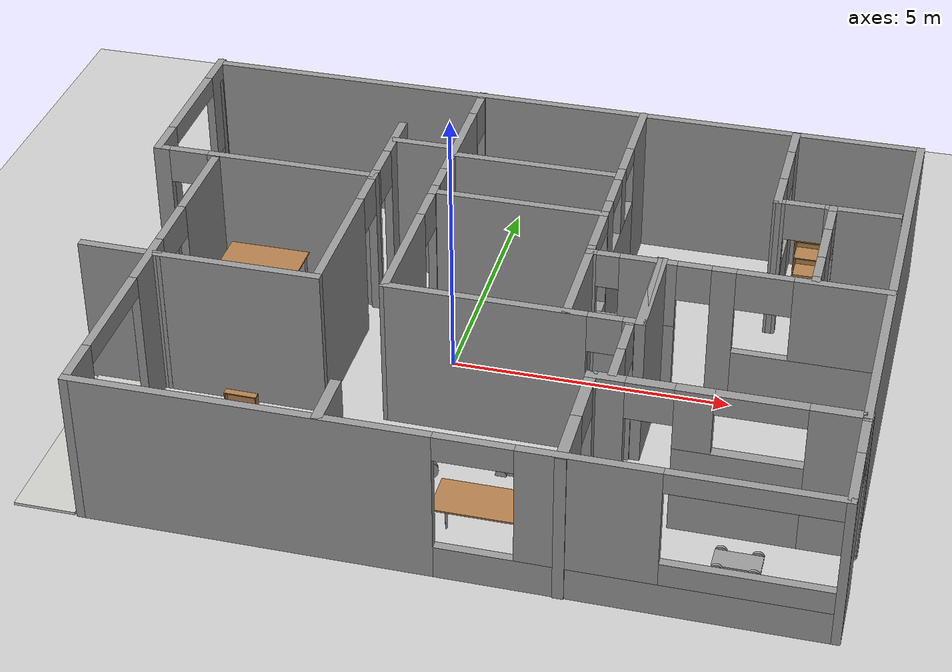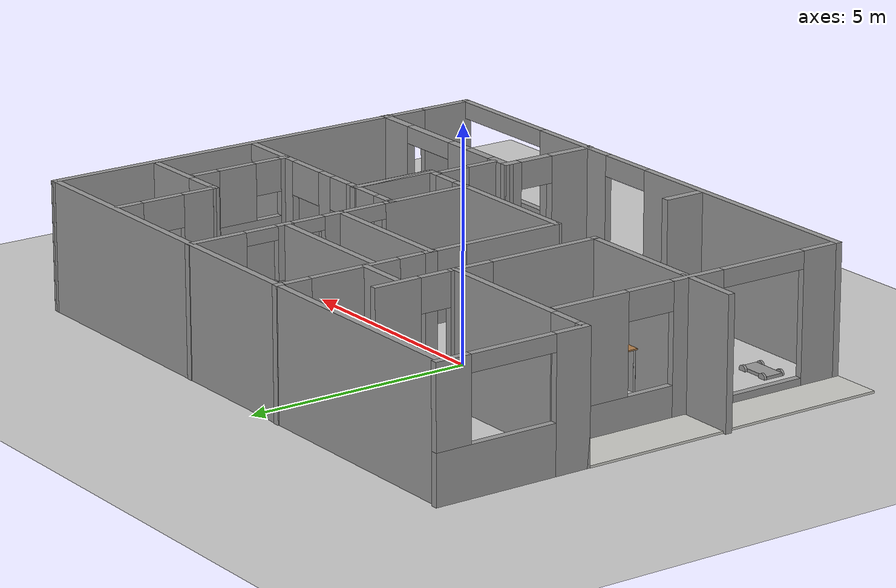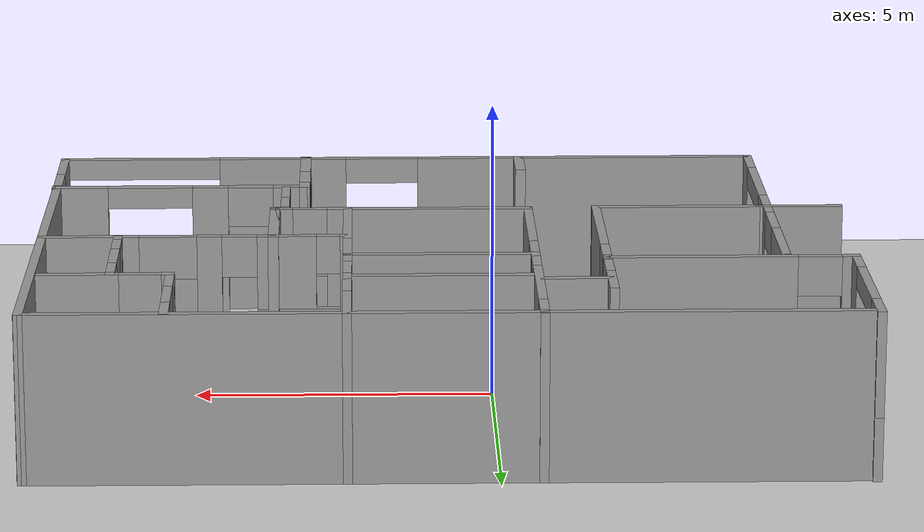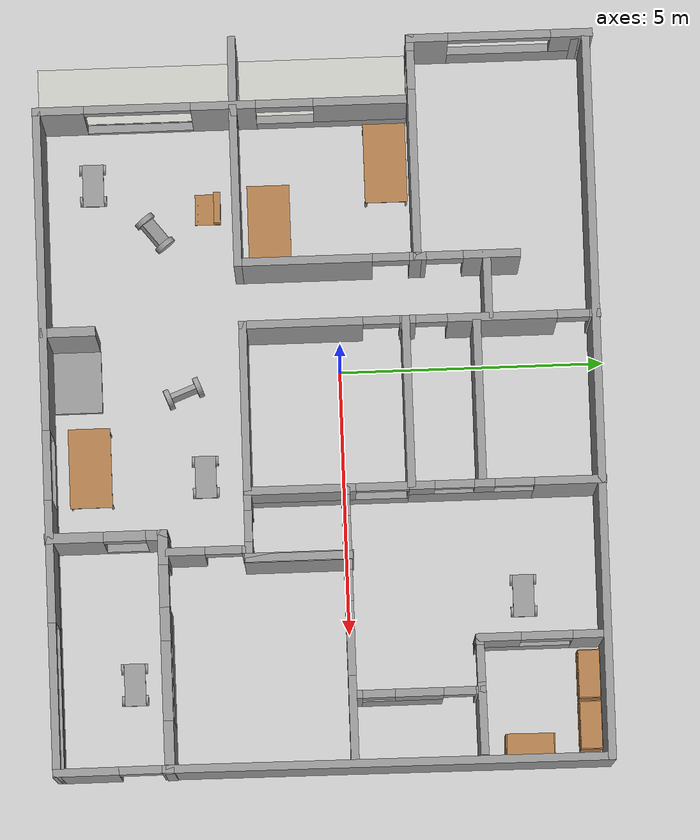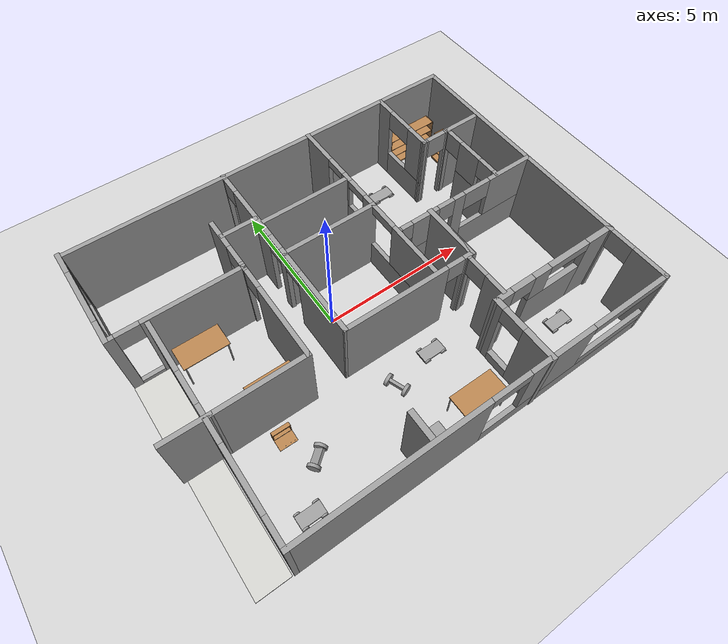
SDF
<sdf version="1.7">
 <world name="default">
  <plugin name="welcome_message" filename="libwelcome_message.so"/>
  <light name="sun" type="directional">
   <pose>0 0 10 0 -0 0</pose>
   <diffuse>0.8 0.8 0.8 1</diffuse>
   <specular>0.2 0.2 0.2 1</specular>
   <attenuation>
    <range>1000</range>
    <constant>0.9</constant>
    <linear>0.01</linear>
    <quadratic>0.001</quadratic>
   </attenuation>
   <direction>-0.5 0.1 -0.9</direction>
   <spot><inner_angle>0</inner_angle><outer_angle>0</outer_angle><falloff>0</falloff></spot>
  </light>
  <model name="ground_plane">
   <static>1</static>
   <link name="link">
    <collision name="collision">
     <geometry><plane><normal>0 0 1</normal><size>100 100</size></plane></geometry>
     <surface>
      <contact><collide_bitmask>65535</collide_bitmask></contact>
      <friction><ode><mu>100</mu><mu2>50</mu2></ode></friction>
     </surface>
    </collision>
    <visual name="visual">
     <cast_shadows>0</cast_shadows>
     <geometry><plane><normal>0 0 1</normal><size>100 100</size></plane></geometry>
     <material>
      <script><uri>file://media/materials/scripts/gazebo.material</uri><name>Gazebo/Grey</name></script>
     </material>
    </visual>
   </link>
  </model>
  <gravity>0 0 -9.8</gravity>
  <magnetic_field>6e-06 2.3e-05 -4.2e-05</magnetic_field>
  <atmosphere type="adiabatic"/>
  <physics type="ode">
   <max_step_size>0.001</max_step_size>
   <real_time_factor>1</real_time_factor>
   <real_time_update_rate>1000</real_time_update_rate>
  </physics>
  <scene><ambient>0.4 0.4 0.4 1</ambient><background>0.7 0.7 0.7 1</background><shadows>1</shadows></scene>
  <audio><device>default</device></audio>
  <spherical_coordinates>
   <surface_model>EARTH_WGS84</surface_model>
   <latitude_deg>0</latitude_deg>
   <longitude_deg>0</longitude_deg>
   <elevation>0</elevation>
   <heading_deg>0</heading_deg>
  </spherical_coordinates>
  <model name="VinHouse">
   <pose>0.77427 -0.337194 0 0 -0 0</pose>
   <link name="Stairs_1">
    <visual name="Stairs_1_Visual_0">
     <pose>-0.742932 -4.64062 0.085 0 -0 0</pose>
     <geometry><box><size>1.16 0.904 0.17</size></box></geometry>
     <material>
      <script><uri>file://media/materials/scripts/gazebo.material</uri><name>Gazebo/Grey</name></script>
      <ambient>1 1 1 1</ambient>
     </material>
     <meta><layer>0</layer></meta>
    </visual>
    <collision name="Stairs_1_Collision_0">
     <geometry><box><size>1.16 0.904 0.17</size></box></geometry>
     <pose>-0.742932 -4.64062 0.085 0 -0 0</pose>
    </collision>
   </link>
   <link name="Stairs_3">
    <visual name="Stairs_3_Visual_0">
     <pose>-6.23499 -3.40621 0.025 0 -0 0</pose>
     <geometry><box><size>1.07387 3.64214 0.05</size></box></geometry>
     <material>
      <script><uri>file://media/materials/scripts/gazebo.material</uri><name>Gazebo/CeilingTiled</name></script>
      <ambient>1 1 1 1</ambient>
     </material>
     <meta><layer>0</layer></meta>
    </visual>
    <collision name="Stairs_3_Collision_0">
     <geometry><box><size>1.07387 3.64214 0.05</size></box></geometry>
     <pose>-6.23499 -3.40621 0.025 0 -0 0</pose>
    </collision>
   </link>
   <link name="Stairs_5">
    <visual name="Stairs_5_Visual_0">
     <pose>-6.23214 0.183373 0.025 0 -0 0</pose>
     <geometry><box><size>1.15359 3.17088 0.05</size></box></geometry>
     <material>
      <script><uri>file://media/materials/scripts/gazebo.material</uri><name>Gazebo/CeilingTiled</name></script>
      <ambient>1 1 1 1</ambient>
     </material>
     <meta><layer>0</layer></meta>
    </visual>
    <collision name="Stairs_5_Collision_0">
     <geometry><box><size>1.15359 3.17088 0.05</size></box></geometry>
     <pose>-6.23214 0.183373 0.025 0 -0 0</pose>
    </collision>
   </link>
   <link name="Wall_11">
    <pose>-5.58322 -1.75049 0 0 -0 1.5708</pose>
    <visual name="Wall_11_Visual_0">
     <pose>-3.01958 0 1.4 0 -0 0</pose>
     <geometry><box><size>0.96085 0.15 2.8</size></box></geometry>
     <material>
      <script><uri>file://media/materials/scripts/gazebo.material</uri><name>Gazebo/Grey</name></script>
      <ambient>1 1 1 1</ambient>
     </material>
     <meta><layer>0</layer></meta>
    </visual>
    <collision name="Wall_11_Collision_0">
     <geometry><box><size>0.96085 0.15 2.8</size></box></geometry>
     <pose>-3.01958 0 1.4 0 -0 0</pose>
    </collision>
    <visual name="Wall_11_Visual_1">
     <pose>0.067031 0 1.4 0 -0 0</pose>
     <geometry><box><size>1.21236 0.15 2.8</size></box></geometry>
     <material>
      <script><uri>file://media/materials/scripts/gazebo.material</uri><name>Gazebo/Grey</name></script>
      <ambient>1 1 1 1</ambient>
     </material>
     <meta><layer>0</layer></meta>
    </visual>
    <collision name="Wall_11_Collision_1">
     <geometry><box><size>1.21236 0.15 2.8</size></box></geometry>
     <pose>0.067031 0 1.4 0 -0 0</pose>
    </collision>
    <visual name="Wall_11_Visual_2">
     <pose>-1.53915 0 0 0 -0 0</pose>
     <geometry><box><size>2 0.15 0.37</size></box></geometry>
     <material>
      <script><uri>file://media/materials/scripts/gazebo.material</uri><name>Gazebo/Grey</name></script>
      <ambient>1 1 1 1</ambient>
     </material>
     <meta><layer>0</layer></meta>
    </visual>
    <collision name="Wall_11_Collision_2">
     <geometry><box><size>2 0.15 0.37</size></box></geometry>
     <pose>-1.53915 0 0 0 -0 0</pose>
    </collision>
    <visual name="Wall_11_Visual_3">
     <pose>2.08661 0 0.35 0 -0 0</pose>
     <geometry><box><size>2.82679 0.15 0.7</size></box></geometry>
     <material>
      <script><uri>file://media/materials/scripts/gazebo.material</uri><name>Gazebo/Grey</name></script>
      <ambient>1 1 1 1</ambient>
     </material>
     <meta><layer>0</layer></meta>
    </visual>
    <collision name="Wall_11_Collision_3">
     <geometry><box><size>2.82679 0.15 0.7</size></box></geometry>
     <pose>2.08661 0 0.35 0 -0 0</pose>
    </collision>
    <visual name="Wall_11_Visual_4">
     <pose>2.62661 0 1.75 0 -0 0</pose>
     <geometry><box><size>1.74679 0.15 2.1</size></box></geometry>
     <material>
      <script><uri>file://media/materials/scripts/gazebo.material</uri><name>Gazebo/Grey</name></script>
      <ambient>1 1 1 1</ambient>
     </material>
     <meta><layer>0</layer></meta>
    </visual>
    <collision name="Wall_11_Collision_4">
     <geometry><box><size>1.74679 0.15 2.1</size></box></geometry>
     <pose>2.62661 0 1.75 0 -0 0</pose>
    </collision>
    <visual name="Wall_11_Visual_5">
     <pose>1.21321 0 2.5 0 -0 0</pose>
     <geometry><box><size>1.08 0.15 0.6</size></box></geometry>
     <material>
      <script><uri>file://media/materials/scripts/gazebo.material</uri><name>Gazebo/Grey</name></script>
      <ambient>1 1 1 1</ambient>
     </material>
     <meta><layer>0</layer></meta>
    </visual>
    <collision name="Wall_11_Collision_5">
     <geometry><box><size>1.08 0.15 0.6</size></box></geometry>
     <pose>1.21321 0 2.5 0 -0 0</pose>
    </collision>
    <visual name="Wall_11_Visual_6">
     <pose>-1.53915 0 2.615 0 -0 0</pose>
     <geometry><box><size>2 0.15 0.37</size></box></geometry>
     <material>
      <script><uri>file://media/materials/scripts/gazebo.material</uri><name>Gazebo/Grey</name></script>
      <ambient>1 1 1 1</ambient>
     </material>
     <meta><layer>0</layer></meta>
    </visual>
    <collision name="Wall_11_Collision_6">
     <geometry><box><size>2 0.15 0.37</size></box></geometry>
     <pose>-1.53915 0 2.615 0 -0 0</pose>
    </collision>
   </link>
   <link name="Wall_13">
    <pose>-4.67222 1.84551 0 0 -0 0</pose>
    <visual name="Wall_13_Visual_0">
     <pose>-1.97199 0 1.4 0 -0 0</pose>
     <geometry><box><size>0.30601 0.15 2.8</size></box></geometry>
     <material>
      <script><uri>file://media/materials/scripts/gazebo.material</uri><name>Gazebo/Grey</name></script>
      <ambient>1 1 1 1</ambient>
     </material>
     <meta><layer>0</layer></meta>
    </visual>
    <collision name="Wall_13_Collision_0">
     <geometry><box><size>0.30601 0.15 2.8</size></box></geometry>
     <pose>-1.97199 0 1.4 0 -0 0</pose>
    </collision>
    <visual name="Wall_13_Visual_1">
     <pose>0.518005 0 1.4 0 -0 0</pose>
     <geometry><box><size>3.21399 0.15 2.8</size></box></geometry>
     <material>
      <script><uri>file://media/materials/scripts/gazebo.material</uri><name>Gazebo/Grey</name></script>
      <ambient>1 1 1 1</ambient>
     </material>
     <meta><layer>0</layer></meta>
    </visual>
    <collision name="Wall_13_Collision_1">
     <geometry><box><size>3.21399 0.15 2.8</size></box></geometry>
     <pose>0.518005 0 1.4 0 -0 0</pose>
    </collision>
    <visual name="Wall_13_Visual_2">
     <pose>-1.45399 0 0 0 -0 0</pose>
     <geometry><box><size>0.73 0.15 0.37</size></box></geometry>
     <material>
      <script><uri>file://media/materials/scripts/gazebo.material</uri><name>Gazebo/Grey</name></script>
      <ambient>1 1 1 1</ambient>
     </material>
     <meta><layer>0</layer></meta>
    </visual>
    <collision name="Wall_13_Collision_2">
     <geometry><box><size>0.73 0.15 0.37</size></box></geometry>
     <pose>-1.45399 0 0 0 -0 0</pose>
    </collision>
    <visual name="Wall_13_Visual_3">
     <pose>-1.45399 0 2.465 0 -0 0</pose>
     <geometry><box><size>0.73 0.15 0.67</size></box></geometry>
     <material>
      <script><uri>file://media/materials/scripts/gazebo.material</uri><name>Gazebo/Grey</name></script>
      <ambient>1 1 1 1</ambient>
     </material>
     <meta><layer>0</layer></meta>
    </visual>
    <collision name="Wall_13_Collision_3">
     <geometry><box><size>0.73 0.15 0.67</size></box></geometry>
     <pose>-1.45399 0 2.465 0 -0 0</pose>
    </collision>
   </link>
   <link name="Wall_14">
    <pose>-2.62222 0.170511 0 0 0 -1.5708</pose>
    <visual name="Wall_14_Visual_0">
     <pose>-1.63879 0 1.4 0 -0 0</pose>
     <geometry><box><size>0.222428 0.15 2.8</size></box></geometry>
     <material>
      <script><uri>file://media/materials/scripts/gazebo.material</uri><name>Gazebo/Grey</name></script>
      <ambient>1 1 1 1</ambient>
     </material>
     <meta><layer>0</layer></meta>
    </visual>
    <collision name="Wall_14_Collision_0">
     <geometry><box><size>0.222428 0.15 2.8</size></box></geometry>
     <pose>-1.63879 0 1.4 0 -0 0</pose>
    </collision>
    <visual name="Wall_14_Visual_1">
     <pose>0.456214 0 1.4 0 -0 0</pose>
     <geometry><box><size>2.58757 0.15 2.8</size></box></geometry>
     <material>
      <script><uri>file://media/materials/scripts/gazebo.material</uri><name>Gazebo/Grey</name></script>
      <ambient>1 1 1 1</ambient>
     </material>
     <meta><layer>0</layer></meta>
    </visual>
    <collision name="Wall_14_Collision_1">
     <geometry><box><size>2.58757 0.15 2.8</size></box></geometry>
     <pose>0.456214 0 1.4 0 -0 0</pose>
    </collision>
    <visual name="Wall_14_Visual_2">
     <pose>-1.18257 0 2.435 0 -0 0</pose>
     <geometry><box><size>0.69 0.15 0.73</size></box></geometry>
     <material>
      <script><uri>file://media/materials/scripts/gazebo.material</uri><name>Gazebo/Grey</name></script>
      <ambient>1 1 1 1</ambient>
     </material>
     <meta><layer>0</layer></meta>
    </visual>
    <collision name="Wall_14_Collision_2">
     <geometry><box><size>0.69 0.15 0.73</size></box></geometry>
     <pose>-1.18257 0 2.435 0 -0 0</pose>
    </collision>
   </link>
   <link name="Wall_15">
    <collision name="Wall_15_Collision">
     <geometry><box><size>2.98282 0.15 2.8</size></box></geometry>
     <pose>0 0 1.4 0 -0 0</pose>
    </collision>
    <visual name="Wall_15_Visual">
     <pose>0 0 1.4 0 -0 0</pose>
     <geometry><box><size>2.98282 0.15 2.8</size></box></geometry>
     <material>
      <script><uri>file://media/materials/scripts/gazebo.material</uri><name>Gazebo/Grey</name></script>
      <ambient>1 1 1 1</ambient>
     </material>
     <meta><layer>0</layer></meta>
    </visual>
    <pose>-4.03822 -1.50449 0 0 -0 3.14159</pose>
   </link>
   <link name="Wall_17">
    <collision name="Wall_17_Collision">
     <geometry><box><size>1.5 0.15 2.8</size></box></geometry>
     <pose>0 0 1.4 0 -0 0</pose>
    </collision>
    <visual name="Wall_17_Visual">
     <pose>0 0 1.4 0 -0 0</pose>
     <geometry><box><size>1.5 0.15 2.8</size></box></geometry>
     <material>
      <script><uri>file://media/materials/scripts/gazebo.material</uri><name>Gazebo/Grey</name></script>
      <ambient>1 1 1 1</ambient>
     </material>
     <meta><layer>0</layer></meta>
    </visual>
    <pose>-6.12922 -1.49599 0 0 -0 3.129</pose>
   </link>
   <link name="Wall_19">
    <pose>-2.62222 2.77051 0 0 -0 1.5708</pose>
    <visual name="Wall_19_Visual_0">
     <pose>-0.879696 0 1.4 0 -0 0</pose>
     <geometry><box><size>0.240608 0.15 2.8</size></box></geometry>
     <material>
      <script><uri>file://media/materials/scripts/gazebo.material</uri><name>Gazebo/Grey</name></script>
      <ambient>1 1 1 1</ambient>
     </material>
     <meta><layer>0</layer></meta>
    </visual>
    <collision name="Wall_19_Collision_0">
     <geometry><box><size>0.240608 0.15 2.8</size></box></geometry>
     <pose>-0.879696 0 1.4 0 -0 0</pose>
    </collision>
    <visual name="Wall_19_Visual_1">
     <pose>0.465304 0 1.4 0 -0 0</pose>
     <geometry><box><size>1.06939 0.15 2.8</size></box></geometry>
     <material>
      <script><uri>file://media/materials/scripts/gazebo.material</uri><name>Gazebo/Grey</name></script>
      <ambient>1 1 1 1</ambient>
     </material>
     <meta><layer>0</layer></meta>
    </visual>
    <collision name="Wall_19_Collision_1">
     <geometry><box><size>1.06939 0.15 2.8</size></box></geometry>
     <pose>0.465304 0 1.4 0 -0 0</pose>
    </collision>
    <visual name="Wall_19_Visual_2">
     <pose>-0.414392 0 2.435 0 -0 0</pose>
     <geometry><box><size>0.69 0.15 0.73</size></box></geometry>
     <material>
      <script><uri>file://media/materials/scripts/gazebo.material</uri><name>Gazebo/Grey</name></script>
      <ambient>1 1 1 1</ambient>
     </material>
     <meta><layer>0</layer></meta>
    </visual>
    <collision name="Wall_19_Collision_2">
     <geometry><box><size>0.69 0.15 0.73</size></box></geometry>
     <pose>-0.414392 0 2.435 0 -0 0</pose>
    </collision>
   </link>
   <link name="Wall_2">
    <pose>0.591778 -5.17549 0 0 -0 0</pose>
    <visual name="Wall_2_Visual_0">
     <pose>-3.22257 0 1.4 0 -0 0</pose>
     <geometry><box><size>6.05486 0.15 2.8</size></box></geometry>
     <material>
      <script><uri>file://media/materials/scripts/gazebo.material</uri><name>Gazebo/Grey</name></script>
      <ambient>1 1 1 1</ambient>
     </material>
     <meta><layer>0</layer></meta>
    </visual>
    <collision name="Wall_2_Collision_0">
     <geometry><box><size>6.05486 0.15 2.8</size></box></geometry>
     <pose>-3.22257 0 1.4 0 -0 0</pose>
    </collision>
    <visual name="Wall_2_Visual_1">
     <pose>3.02743 0 0.305 0 -0 0</pose>
     <geometry><box><size>6.44514 0.15 0.61</size></box></geometry>
     <material>
      <script><uri>file://media/materials/scripts/gazebo.material</uri><name>Gazebo/Grey</name></script>
      <ambient>1 1 1 1</ambient>
     </material>
     <meta><layer>0</layer></meta>
    </visual>
    <collision name="Wall_2_Collision_1">
     <geometry><box><size>6.44514 0.15 0.61</size></box></geometry>
     <pose>3.02743 0 0.305 0 -0 0</pose>
    </collision>
    <visual name="Wall_2_Visual_2">
     <pose>2.24473 0 1.705 0 -0 0</pose>
     <geometry><box><size>2.27975 0.15 2.19</size></box></geometry>
     <material>
      <script><uri>file://media/materials/scripts/gazebo.material</uri><name>Gazebo/Grey</name></script>
      <ambient>1 1 1 1</ambient>
     </material>
     <meta><layer>0</layer></meta>
    </visual>
    <collision name="Wall_2_Collision_2">
     <geometry><box><size>2.27975 0.15 2.19</size></box></geometry>
     <pose>2.24473 0 1.705 0 -0 0</pose>
    </collision>
    <visual name="Wall_2_Visual_3">
     <pose>4.81731 0 0.82 0 -0 0</pose>
     <geometry><box><size>2.86539 0.15 0.42</size></box></geometry>
     <material>
      <script><uri>file://media/materials/scripts/gazebo.material</uri><name>Gazebo/Grey</name></script>
      <ambient>1 1 1 1</ambient>
     </material>
     <meta><layer>0</layer></meta>
    </visual>
    <collision name="Wall_2_Collision_3">
     <geometry><box><size>2.86539 0.15 0.42</size></box></geometry>
     <pose>4.81731 0 0.82 0 -0 0</pose>
    </collision>
    <visual name="Wall_2_Visual_4">
     <pose>6.2023 0 1.915 0 -0 0</pose>
     <geometry><box><size>0.095389 0.15 1.77</size></box></geometry>
     <material>
      <script><uri>file://media/materials/scripts/gazebo.material</uri><name>Gazebo/Grey</name></script>
      <ambient>1 1 1 1</ambient>
     </material>
     <meta><layer>0</layer></meta>
    </visual>
    <collision name="Wall_2_Collision_4">
     <geometry><box><size>0.095389 0.15 1.77</size></box></geometry>
     <pose>6.2023 0 1.915 0 -0 0</pose>
    </collision>
    <visual name="Wall_2_Visual_5">
     <pose>0.454859 0 2.575 0 -0 0</pose>
     <geometry><box><size>1.3 0.15 0.45</size></box></geometry>
     <material>
      <script><uri>file://media/materials/scripts/gazebo.material</uri><name>Gazebo/Grey</name></script>
      <ambient>1 1 1 1</ambient>
     </material>
     <meta><layer>0</layer></meta>
    </visual>
    <collision name="Wall_2_Collision_5">
     <geometry><box><size>1.3 0.15 0.45</size></box></geometry>
     <pose>0.454859 0 2.575 0 -0 0</pose>
    </collision>
    <visual name="Wall_2_Visual_6">
     <pose>4.76961 0 2.615 0 -0 0</pose>
     <geometry><box><size>2.77 0.15 0.37</size></box></geometry>
     <material>
      <script><uri>file://media/materials/scripts/gazebo.material</uri><name>Gazebo/Grey</name></script>
      <ambient>1 1 1 1</ambient>
     </material>
     <meta><layer>0</layer></meta>
    </visual>
    <collision name="Wall_2_Collision_6">
     <geometry><box><size>2.77 0.15 0.37</size></box></geometry>
     <pose>4.76961 0 2.615 0 -0 0</pose>
    </collision>
   </link>
   <link name="Wall_21">
    <collision name="Wall_21_Collision">
     <geometry><box><size>1.25 0.15 2.8</size></box></geometry>
     <pose>0 0 1.4 0 -0 0</pose>
    </collision>
    <visual name="Wall_21_Visual">
     <pose>0 0 1.4 0 -0 0</pose>
     <geometry><box><size>1.25 0.15 2.8</size></box></geometry>
     <material>
      <script><uri>file://media/materials/scripts/gazebo.material</uri><name>Gazebo/Grey</name></script>
      <ambient>1 1 1 1</ambient>
     </material>
     <meta><layer>0</layer></meta>
    </visual>
    <pose>-2.03822 3.13551 0 0 -0 0</pose>
   </link>
   <link name="Wall_23">
    <pose>-1.44622 1.84351 0 0 0 -1.5708</pose>
    <visual name="Wall_23_Visual_0">
     <pose>-3.27076 0 1.4 0 -0 0</pose>
     <geometry><box><size>0.208484 0.15 2.8</size></box></geometry>
     <material>
      <script><uri>file://media/materials/scripts/gazebo.material</uri><name>Gazebo/Grey</name></script>
      <ambient>1 1 1 1</ambient>
     </material>
     <meta><layer>0</layer></meta>
    </visual>
    <collision name="Wall_23_Collision_0">
     <geometry><box><size>0.208484 0.15 2.8</size></box></geometry>
     <pose>-3.27076 0 1.4 0 -0 0</pose>
    </collision>
    <visual name="Wall_23_Visual_1">
     <pose>-1.54241 0 1.4 0 -0 0</pose>
     <geometry><box><size>2.04821 0.15 2.8</size></box></geometry>
     <material>
      <script><uri>file://media/materials/scripts/gazebo.material</uri><name>Gazebo/Grey</name></script>
      <ambient>1 1 1 1</ambient>
     </material>
     <meta><layer>0</layer></meta>
    </visual>
    <collision name="Wall_23_Collision_1">
     <geometry><box><size>2.04821 0.15 2.8</size></box></geometry>
     <pose>-1.54241 0 1.4 0 -0 0</pose>
    </collision>
    <visual name="Wall_23_Visual_2">
     <pose>0.218536 0 1.4 0 -0 0</pose>
     <geometry><box><size>0.293673 0.15 2.8</size></box></geometry>
     <material>
      <script><uri>file://media/materials/scripts/gazebo.material</uri><name>Gazebo/Grey</name></script>
      <ambient>1 1 1 1</ambient>
     </material>
     <meta><layer>0</layer></meta>
    </visual>
    <collision name="Wall_23_Collision_2">
     <geometry><box><size>0.293673 0.15 2.8</size></box></geometry>
     <pose>0.218536 0 1.4 0 -0 0</pose>
    </collision>
    <visual name="Wall_23_Visual_3">
     <pose>2.21519 0 1.4 0 -0 0</pose>
     <geometry><box><size>2.31963 0.15 2.8</size></box></geometry>
     <material>
      <script><uri>file://media/materials/scripts/gazebo.material</uri><name>Gazebo/Grey</name></script>
      <ambient>1 1 1 1</ambient>
     </material>
     <meta><layer>0</layer></meta>
    </visual>
    <collision name="Wall_23_Collision_3">
     <geometry><box><size>2.31963 0.15 2.8</size></box></geometry>
     <pose>2.21519 0 1.4 0 -0 0</pose>
    </collision>
    <visual name="Wall_23_Visual_4">
     <pose>-2.86652 0 2.44 0 -0 0</pose>
     <geometry><box><size>0.6 0.15 0.72</size></box></geometry>
     <material>
      <script><uri>file://media/materials/scripts/gazebo.material</uri><name>Gazebo/Grey</name></script>
      <ambient>1 1 1 1</ambient>
     </material>
     <meta><layer>0</layer></meta>
    </visual>
    <collision name="Wall_23_Collision_4">
     <geometry><box><size>0.6 0.15 0.72</size></box></geometry>
     <pose>-2.86652 0 2.44 0 -0 0</pose>
    </collision>
    <visual name="Wall_23_Visual_5">
     <pose>-0.223301 0 2.45 0 -0 0</pose>
     <geometry><box><size>0.59 0.15 0.7</size></box></geometry>
     <material>
      <script><uri>file://media/materials/scripts/gazebo.material</uri><name>Gazebo/Grey</name></script>
      <ambient>1 1 1 1</ambient>
     </material>
     <meta><layer>0</layer></meta>
    </visual>
    <collision name="Wall_23_Collision_5">
     <geometry><box><size>0.59 0.15 0.7</size></box></geometry>
     <pose>-0.223301 0 2.45 0 -0 0</pose>
    </collision>
    <visual name="Wall_23_Visual_6">
     <pose>0.710372 0 2.45 0 -0 0</pose>
     <geometry><box><size>0.69 0.15 0.7</size></box></geometry>
     <material>
      <script><uri>file://media/materials/scripts/gazebo.material</uri><name>Gazebo/Grey</name></script>
      <ambient>1 1 1 1</ambient>
     </material>
     <meta><layer>0</layer></meta>
    </visual>
    <collision name="Wall_23_Collision_6">
     <geometry><box><size>0.69 0.15 0.7</size></box></geometry>
     <pose>0.710372 0 2.45 0 -0 0</pose>
    </collision>
   </link>
   <link name="Wall_24">
    <pose>0.728778 -1.46799 0 0 0 -0.005287</pose>
    <visual name="Wall_24_Visual_0">
     <pose>-0.482727 0 1.4 0 -0 0</pose>
     <geometry><box><size>3.53455 0.15 2.8</size></box></geometry>
     <material>
      <script><uri>file://media/materials/scripts/gazebo.material</uri><name>Gazebo/Grey</name></script>
      <ambient>1 1 1 1</ambient>
     </material>
     <meta><layer>0</layer></meta>
    </visual>
    <collision name="Wall_24_Collision_0">
     <geometry><box><size>3.53455 0.15 2.8</size></box></geometry>
     <pose>-0.482727 0 1.4 0 -0 0</pose>
    </collision>
    <visual name="Wall_24_Visual_1">
     <pose>2.06227 0 1.4 0 -0 0</pose>
     <geometry><box><size>0.375454 0.15 2.8</size></box></geometry>
     <material>
      <script><uri>file://media/materials/scripts/gazebo.material</uri><name>Gazebo/Grey</name></script>
      <ambient>1 1 1 1</ambient>
     </material>
     <meta><layer>0</layer></meta>
    </visual>
    <collision name="Wall_24_Collision_1">
     <geometry><box><size>0.375454 0.15 2.8</size></box></geometry>
     <pose>2.06227 0 1.4 0 -0 0</pose>
    </collision>
    <visual name="Wall_24_Visual_2">
     <pose>1.57955 0 2.45 0 -0 0</pose>
     <geometry><box><size>0.59 0.15 0.7</size></box></geometry>
     <material>
      <script><uri>file://media/materials/scripts/gazebo.material</uri><name>Gazebo/Grey</name></script>
      <ambient>1 1 1 1</ambient>
     </material>
     <meta><layer>0</layer></meta>
    </visual>
    <collision name="Wall_24_Collision_2">
     <geometry><box><size>0.59 0.15 0.7</size></box></geometry>
     <pose>1.57955 0 2.45 0 -0 0</pose>
    </collision>
   </link>
   <link name="Wall_25">
    <collision name="Wall_25_Collision">
     <geometry><box><size>2 0.15 2.8</size></box></geometry>
     <pose>0 0 1.4 0 -0 0</pose>
    </collision>
    <visual name="Wall_25_Visual">
     <pose>0 0 1.4 0 -0 0</pose>
     <geometry><box><size>2 0.15 2.8</size></box></geometry>
     <material>
      <script><uri>file://media/materials/scripts/gazebo.material</uri><name>Gazebo/Grey</name></script>
      <ambient>1 1 1 1</ambient>
     </material>
     <meta><layer>0</layer></meta>
    </visual>
    <pose>2.90378 -0.554489 0 0 -0 1.5708</pose>
   </link>
   <link name="Wall_28">
    <collision name="Wall_28_Collision">
     <geometry><box><size>0.15 0.15 2.5</size></box></geometry>
     <pose>0 0 1.25 0 -0 0</pose>
    </collision>
    <visual name="Wall_28_Visual">
     <pose>0 0 1.25 0 -0 0</pose>
     <geometry><box><size>0.15 0.15 2.5</size></box></geometry>
     <material>
      <script><uri>file://media/materials/scripts/gazebo.material</uri><name>Gazebo/Grey</name></script>
      <ambient>1 1 1 1</ambient>
     </material>
     <meta><layer>0</layer></meta>
    </visual>
    <pose>-6.722 4.9453 0 0 -0 0</pose>
   </link>
   <link name="Wall_3">
    <pose>6.76441 -4.12685 0 0 -0 1.57306</pose>
    <visual name="Wall_3_Visual_0">
     <pose>-0.509705 0 1.4 0 -0 0</pose>
     <geometry><box><size>1.22849 0.15 2.8</size></box></geometry>
     <material>
      <script><uri>file://media/materials/scripts/gazebo.material</uri><name>Gazebo/Grey</name></script>
      <ambient>1 1 1 1</ambient>
     </material>
     <meta><layer>0</layer></meta>
    </visual>
    <collision name="Wall_3_Collision_0">
     <geometry><box><size>1.22849 0.15 2.8</size></box></geometry>
     <pose>-0.509705 0 1.4 0 -0 0</pose>
    </collision>
    <visual name="Wall_3_Visual_1">
     <pose>1.01425 0 1.4 0 -0 0</pose>
     <geometry><box><size>0.21941 0.15 2.8</size></box></geometry>
     <material>
      <script><uri>file://media/materials/scripts/gazebo.material</uri><name>Gazebo/Grey</name></script>
      <ambient>1 1 1 1</ambient>
     </material>
     <meta><layer>0</layer></meta>
    </visual>
    <collision name="Wall_3_Collision_1">
     <geometry><box><size>0.21941 0.15 2.8</size></box></geometry>
     <pose>1.01425 0 1.4 0 -0 0</pose>
    </collision>
    <visual name="Wall_3_Visual_2">
     <pose>0.504542 0 2.445 0 -0 0</pose>
     <geometry><box><size>0.8 0.15 0.71</size></box></geometry>
     <material>
      <script><uri>file://media/materials/scripts/gazebo.material</uri><name>Gazebo/Grey</name></script>
      <ambient>1 1 1 1</ambient>
     </material>
     <meta><layer>0</layer></meta>
    </visual>
    <collision name="Wall_3_Collision_2">
     <geometry><box><size>0.8 0.15 0.71</size></box></geometry>
     <pose>0.504542 0 2.445 0 -0 0</pose>
    </collision>
   </link>
   <link name="Wall_33">
    <pose>-6.72222 3.52051 0 0 -0 1.5708</pose>
    <visual name="Wall_33_Visual_0">
     <pose>-1.35388 0 1.4 0 -0 0</pose>
     <geometry><box><size>0.792235 0.15 2.8</size></box></geometry>
     <material>
      <script><uri>file://media/materials/scripts/gazebo.material</uri><name>Gazebo/Grey</name></script>
      <ambient>1 1 1 1</ambient>
     </material>
     <meta><layer>0</layer></meta>
    </visual>
    <collision name="Wall_33_Collision_0">
     <geometry><box><size>0.792235 0.15 2.8</size></box></geometry>
     <pose>-1.35388 0 1.4 0 -0 0</pose>
    </collision>
    <visual name="Wall_33_Visual_1">
     <pose>0.396117 0 0.53 0 -0 0</pose>
     <geometry><box><size>2.70777 0.15 1.06</size></box></geometry>
     <material>
      <script><uri>file://media/materials/scripts/gazebo.material</uri><name>Gazebo/Grey</name></script>
      <ambient>1 1 1 1</ambient>
     </material>
     <meta><layer>0</layer></meta>
    </visual>
    <collision name="Wall_33_Collision_1">
     <geometry><box><size>2.70777 0.15 1.06</size></box></geometry>
     <pose>0.396117 0 0.53 0 -0 0</pose>
    </collision>
    <visual name="Wall_33_Visual_2">
     <pose>1.35612 0 1.93 0 -0 0</pose>
     <geometry><box><size>0.787765 0.15 1.74</size></box></geometry>
     <material>
      <script><uri>file://media/materials/scripts/gazebo.material</uri><name>Gazebo/Grey</name></script>
      <ambient>1 1 1 1</ambient>
     </material>
     <meta><layer>0</layer></meta>
    </visual>
    <collision name="Wall_33_Collision_2">
     <geometry><box><size>0.787765 0.15 1.74</size></box></geometry>
     <pose>1.35612 0 1.93 0 -0 0</pose>
    </collision>
    <visual name="Wall_33_Visual_3">
     <pose>0.002235 0 2.62 0 -0 0</pose>
     <geometry><box><size>1.92 0.15 0.36</size></box></geometry>
     <material>
      <script><uri>file://media/materials/scripts/gazebo.material</uri><name>Gazebo/Grey</name></script>
      <ambient>1 1 1 1</ambient>
     </material>
     <meta><layer>0</layer></meta>
    </visual>
    <collision name="Wall_33_Collision_3">
     <geometry><box><size>1.92 0.15 0.36</size></box></geometry>
     <pose>0.002235 0 2.62 0 -0 0</pose>
    </collision>
   </link>
   <link name="Wall_35">
    <collision name="Wall_35_Collision">
     <geometry><box><size>8.3391 0.15 2.8</size></box></geometry>
     <pose>0 0 1.4 0 -0 0</pose>
    </collision>
    <visual name="Wall_35_Visual">
     <pose>0 0 1.4 0 -0 0</pose>
     <geometry><box><size>8.3391 0.15 2.8</size></box></geometry>
     <material>
      <script><uri>file://media/materials/scripts/gazebo.material</uri><name>Gazebo/Grey</name></script>
      <ambient>1 1 1 1</ambient>
     </material>
     <meta><layer>0</layer></meta>
    </visual>
    <pose>6.78474 1.0163 0 0 -0 1.56591</pose>
   </link>
   <link name="Wall_36">
    <collision name="Wall_36_Collision">
     <geometry><box><size>13.5353 0.15 2.8</size></box></geometry>
     <pose>0 0 1.4 0 -0 0</pose>
    </collision>
    <visual name="Wall_36_Visual">
     <pose>0 0 1.4 0 -0 0</pose>
     <geometry><box><size>13.5353 0.15 2.8</size></box></geometry>
     <material>
      <script><uri>file://media/materials/scripts/gazebo.material</uri><name>Gazebo/Grey</name></script>
      <ambient>1 1 1 1</ambient>
     </material>
     <meta><layer>0</layer></meta>
    </visual>
    <pose>0.109405 5.12366 0 0 -0 3.13967</pose>
   </link>
   <link name="Wall_38">
    <pose>1.6599 1.83451 0 0 0 -1.5708</pose>
    <visual name="Wall_38_Visual_0">
     <pose>-2.70534 0 1.4 0 -0 0</pose>
     <geometry><box><size>1.33931 0.15 2.8</size></box></geometry>
     <material>
      <script><uri>file://media/materials/scripts/gazebo.material</uri><name>Gazebo/Grey</name></script>
      <ambient>1 1 1 1</ambient>
     </material>
     <meta><layer>0</layer></meta>
    </visual>
    <collision name="Wall_38_Collision_0">
     <geometry><box><size>1.33931 0.15 2.8</size></box></geometry>
     <pose>-2.70534 0 1.4 0 -0 0</pose>
    </collision>
    <visual name="Wall_38_Visual_1">
     <pose>-0.868631 0 0.83 0 -0 0</pose>
     <geometry><box><size>2.33411 0.15 1.66</size></box></geometry>
     <material>
      <script><uri>file://media/materials/scripts/gazebo.material</uri><name>Gazebo/Grey</name></script>
      <ambient>1 1 1 1</ambient>
     </material>
     <meta><layer>0</layer></meta>
    </visual>
    <collision name="Wall_38_Collision_1">
     <geometry><box><size>2.33411 0.15 1.66</size></box></geometry>
     <pose>-0.868631 0 0.83 0 -0 0</pose>
    </collision>
    <visual name="Wall_38_Visual_2">
     <pose>1.83671 0 0.495 0 -0 0</pose>
     <geometry><box><size>3.07658 0.15 0.99</size></box></geometry>
     <material>
      <script><uri>file://media/materials/scripts/gazebo.material</uri><name>Gazebo/Grey</name></script>
      <ambient>1 1 1 1</ambient>
     </material>
     <meta><layer>0</layer></meta>
    </visual>
    <collision name="Wall_38_Collision_2">
     <geometry><box><size>3.07658 0.15 0.99</size></box></geometry>
     <pose>1.83671 0 0.495 0 -0 0</pose>
    </collision>
    <visual name="Wall_38_Visual_3">
     <pose>2.33171 0 1.895 0 -0 0</pose>
     <geometry><box><size>2.08658 0.15 1.81</size></box></geometry>
     <material>
      <script><uri>file://media/materials/scripts/gazebo.material</uri><name>Gazebo/Grey</name></script>
      <ambient>1 1 1 1</ambient>
     </material>
     <meta><layer>0</layer></meta>
    </visual>
    <collision name="Wall_38_Collision_3">
     <geometry><box><size>2.08658 0.15 1.81</size></box></geometry>
     <pose>2.33171 0 1.895 0 -0 0</pose>
    </collision>
    <visual name="Wall_38_Visual_4">
     <pose>-1.1068 0 2.23 0 -0 0</pose>
     <geometry><box><size>0.377778 0.15 1.14</size></box></geometry>
     <material>
      <script><uri>file://media/materials/scripts/gazebo.material</uri><name>Gazebo/Grey</name></script>
      <ambient>1 1 1 1</ambient>
     </material>
     <meta><layer>0</layer></meta>
    </visual>
    <collision name="Wall_38_Collision_4">
     <geometry><box><size>0.377778 0.15 1.14</size></box></geometry>
     <pose>-1.1068 0 2.23 0 -0 0</pose>
    </collision>
    <visual name="Wall_38_Visual_5">
     <pose>0.060258 0 2.23 0 -0 0</pose>
     <geometry><box><size>0.476333 0.15 1.14</size></box></geometry>
     <material>
      <script><uri>file://media/materials/scripts/gazebo.material</uri><name>Gazebo/Grey</name></script>
      <ambient>1 1 1 1</ambient>
     </material>
     <meta><layer>0</layer></meta>
    </visual>
    <collision name="Wall_38_Collision_5">
     <geometry><box><size>0.476333 0.15 1.14</size></box></geometry>
     <pose>0.060258 0 2.23 0 -0 0</pose>
    </collision>
    <visual name="Wall_38_Visual_6">
     <pose>0.793424 0 2.64 0 -0 0</pose>
     <geometry><box><size>0.99 0.15 0.32</size></box></geometry>
     <material>
      <script><uri>file://media/materials/scripts/gazebo.material</uri><name>Gazebo/Grey</name></script>
      <ambient>1 1 1 1</ambient>
     </material>
     <meta><layer>0</layer></meta>
    </visual>
    <collision name="Wall_38_Collision_6">
     <geometry><box><size>0.99 0.15 0.32</size></box></geometry>
     <pose>0.793424 0 2.64 0 -0 0</pose>
    </collision>
    <visual name="Wall_38_Visual_7">
     <pose>-1.66569 0 2.66 0 -0 0</pose>
     <geometry><box><size>0.74 0.15 0.28</size></box></geometry>
     <material>
      <script><uri>file://media/materials/scripts/gazebo.material</uri><name>Gazebo/Grey</name></script>
      <ambient>1 1 1 1</ambient>
     </material>
     <meta><layer>0</layer></meta>
    </visual>
    <collision name="Wall_38_Collision_7">
     <geometry><box><size>0.74 0.15 0.28</size></box></geometry>
     <pose>-1.66569 0 2.66 0 -0 0</pose>
    </collision>
    <visual name="Wall_38_Visual_8">
     <pose>-0.547909 0 2.66 0 -0 0</pose>
     <geometry><box><size>0.74 0.15 0.28</size></box></geometry>
     <material>
      <script><uri>file://media/materials/scripts/gazebo.material</uri><name>Gazebo/Grey</name></script>
      <ambient>1 1 1 1</ambient>
     </material>
     <meta><layer>0</layer></meta>
    </visual>
    <collision name="Wall_38_Collision_8">
     <geometry><box><size>0.74 0.15 0.28</size></box></geometry>
     <pose>-0.547909 0 2.66 0 -0 0</pose>
    </collision>
   </link>
   <link name="Wall_4">
    <pose>4.58941 -3.07685 0 0 -0 3.14097</pose>
    <visual name="Wall_4_Visual_0">
     <pose>-1.77354 0 1.4 0 -0 0</pose>
     <geometry><box><size>0.988165 0.19 2.8</size></box></geometry>
     <material>
      <script><uri>file://media/materials/scripts/gazebo.material</uri><name>Gazebo/Grey</name></script>
      <ambient>1 1 1 1</ambient>
     </material>
     <meta><layer>0</layer></meta>
    </visual>
    <collision name="Wall_4_Collision_0">
     <geometry><box><size>0.988165 0.19 2.8</size></box></geometry>
     <pose>-1.77354 0 1.4 0 -0 0</pose>
    </collision>
    <visual name="Wall_4_Visual_1">
     <pose>1.94252 0 1.4 0 -0 0</pose>
     <geometry><box><size>0.650208 0.19 2.8</size></box></geometry>
     <material>
      <script><uri>file://media/materials/scripts/gazebo.material</uri><name>Gazebo/Grey</name></script>
      <ambient>1 1 1 1</ambient>
     </material>
     <meta><layer>0</layer></meta>
    </visual>
    <collision name="Wall_4_Collision_1">
     <geometry><box><size>0.650208 0.19 2.8</size></box></geometry>
     <pose>1.94252 0 1.4 0 -0 0</pose>
    </collision>
    <visual name="Wall_4_Visual_2">
     <pose>-0.226022 0 0.82 0 -0 0</pose>
     <geometry><box><size>2.10688 0.19 1.64</size></box></geometry>
     <material>
      <script><uri>file://media/materials/scripts/gazebo.material</uri><name>Gazebo/Grey</name></script>
      <ambient>1 1 1 1</ambient>
     </material>
     <meta><layer>0</layer></meta>
    </visual>
    <collision name="Wall_4_Collision_2">
     <geometry><box><size>2.10688 0.19 1.64</size></box></geometry>
     <pose>-0.226022 0 0.82 0 -0 0</pose>
    </collision>
    <visual name="Wall_4_Visual_3">
     <pose>0.513978 0 2.22 0 -0 0</pose>
     <geometry><box><size>0.626881 0.19 1.16</size></box></geometry>
     <material>
      <script><uri>file://media/materials/scripts/gazebo.material</uri><name>Gazebo/Grey</name></script>
      <ambient>1 1 1 1</ambient>
     </material>
     <meta><layer>0</layer></meta>
    </visual>
    <collision name="Wall_4_Collision_3">
     <geometry><box><size>0.626881 0.19 1.16</size></box></geometry>
     <pose>0.513978 0 2.22 0 -0 0</pose>
    </collision>
    <visual name="Wall_4_Visual_4">
     <pose>1.22242 0 2.45 0 -0 0</pose>
     <geometry><box><size>0.79 0.19 0.7</size></box></geometry>
     <material>
      <script><uri>file://media/materials/scripts/gazebo.material</uri><name>Gazebo/Grey</name></script>
      <ambient>1 1 1 1</ambient>
     </material>
     <meta><layer>0</layer></meta>
    </visual>
    <collision name="Wall_4_Collision_4">
     <geometry><box><size>0.79 0.19 0.7</size></box></geometry>
     <pose>1.22242 0 2.45 0 -0 0</pose>
    </collision>
    <visual name="Wall_4_Visual_5">
     <pose>-0.539462 0 2.615 0 -0 0</pose>
     <geometry><box><size>1.48 0.19 0.37</size></box></geometry>
     <material>
      <script><uri>file://media/materials/scripts/gazebo.material</uri><name>Gazebo/Grey</name></script>
      <ambient>1 1 1 1</ambient>
     </material>
     <meta><layer>0</layer></meta>
    </visual>
    <collision name="Wall_4_Collision_5">
     <geometry><box><size>1.48 0.19 0.37</size></box></geometry>
     <pose>-0.539462 0 2.615 0 -0 0</pose>
    </collision>
   </link>
   <link name="Wall_40">
    <pose>4.21478 0.354511 0 0 -0 0</pose>
    <visual name="Wall_40_Visual_0">
     <pose>-2.52811 0 1.4 0 -0 0</pose>
     <geometry><box><size>0.193785 0.15 2.8</size></box></geometry>
     <material>
      <script><uri>file://media/materials/scripts/gazebo.material</uri><name>Gazebo/Grey</name></script>
      <ambient>1 1 1 1</ambient>
     </material>
     <meta><layer>0</layer></meta>
    </visual>
    <collision name="Wall_40_Collision_0">
     <geometry><box><size>0.193785 0.15 2.8</size></box></geometry>
     <pose>-2.52811 0 1.4 0 -0 0</pose>
    </collision>
    <visual name="Wall_40_Visual_1">
     <pose>-0.241553 0 1.4 0 -0 0</pose>
     <geometry><box><size>0.418543 0.15 2.8</size></box></geometry>
     <material>
      <script><uri>file://media/materials/scripts/gazebo.material</uri><name>Gazebo/Grey</name></script>
      <ambient>1 1 1 1</ambient>
     </material>
     <meta><layer>0</layer></meta>
    </visual>
    <collision name="Wall_40_Collision_1">
     <geometry><box><size>0.418543 0.15 2.8</size></box></geometry>
     <pose>-0.241553 0 1.4 0 -0 0</pose>
    </collision>
    <visual name="Wall_40_Visual_2">
     <pose>-1.73602 0 0.77 0 -0 0</pose>
     <geometry><box><size>1.39039 0.15 1.54</size></box></geometry>
     <material>
      <script><uri>file://media/materials/scripts/gazebo.material</uri><name>Gazebo/Grey</name></script>
      <ambient>1 1 1 1</ambient>
     </material>
     <meta><layer>0</layer></meta>
    </visual>
    <collision name="Wall_40_Collision_2">
     <geometry><box><size>1.39039 0.15 1.54</size></box></geometry>
     <pose>-1.73602 0 0.77 0 -0 0</pose>
    </collision>
    <visual name="Wall_40_Visual_3">
     <pose>1.29636 0 0.585 0 -0 0</pose>
     <geometry><box><size>2.65728 0.15 1.17</size></box></geometry>
     <material>
      <script><uri>file://media/materials/scripts/gazebo.material</uri><name>Gazebo/Grey</name></script>
      <ambient>1 1 1 1</ambient>
     </material>
     <meta><layer>0</layer></meta>
    </visual>
    <collision name="Wall_40_Collision_3">
     <geometry><box><size>2.65728 0.15 1.17</size></box></geometry>
     <pose>1.29636 0 0.585 0 -0 0</pose>
    </collision>
    <visual name="Wall_40_Visual_4">
     <pose>1.78136 0 1.985 0 -0 0</pose>
     <geometry><box><size>1.68728 0.15 1.63</size></box></geometry>
     <material>
      <script><uri>file://media/materials/scripts/gazebo.material</uri><name>Gazebo/Grey</name></script>
      <ambient>1 1 1 1</ambient>
     </material>
     <meta><layer>0</layer></meta>
    </visual>
    <collision name="Wall_40_Collision_4">
     <geometry><box><size>1.68728 0.15 1.63</size></box></geometry>
     <pose>1.78136 0 1.985 0 -0 0</pose>
    </collision>
    <visual name="Wall_40_Visual_5">
     <pose>-1.53602 0 2.17 0 -0 0</pose>
     <geometry><box><size>0.990391 0.15 1.26</size></box></geometry>
     <material>
      <script><uri>file://media/materials/scripts/gazebo.material</uri><name>Gazebo/Grey</name></script>
      <ambient>1 1 1 1</ambient>
     </material>
     <meta><layer>0</layer></meta>
    </visual>
    <collision name="Wall_40_Collision_5">
     <geometry><box><size>0.990391 0.15 1.26</size></box></geometry>
     <pose>-1.53602 0 2.17 0 -0 0</pose>
    </collision>
    <visual name="Wall_40_Visual_6">
     <pose>0.452719 0 2.435 0 -0 0</pose>
     <geometry><box><size>0.97 0.15 0.73</size></box></geometry>
     <material>
      <script><uri>file://media/materials/scripts/gazebo.material</uri><name>Gazebo/Grey</name></script>
      <ambient>1 1 1 1</ambient>
     </material>
     <meta><layer>0</layer></meta>
    </visual>
    <collision name="Wall_40_Collision_6">
     <geometry><box><size>0.97 0.15 0.73</size></box></geometry>
     <pose>0.452719 0 2.435 0 -0 0</pose>
    </collision>
    <visual name="Wall_40_Visual_7">
     <pose>-0.745824 0 2.45 0 -0 0</pose>
     <geometry><box><size>0.59 0.15 0.7</size></box></geometry>
     <material>
      <script><uri>file://media/materials/scripts/gazebo.material</uri><name>Gazebo/Grey</name></script>
      <ambient>1 1 1 1</ambient>
     </material>
     <meta><layer>0</layer></meta>
    </visual>
    <collision name="Wall_40_Collision_7">
     <geometry><box><size>0.59 0.15 0.7</size></box></geometry>
     <pose>-0.745824 0 2.45 0 -0 0</pose>
    </collision>
    <visual name="Wall_40_Visual_8">
     <pose>-2.23122 0 2.475 0 -0 0</pose>
     <geometry><box><size>0.4 0.15 0.65</size></box></geometry>
     <material>
      <script><uri>file://media/materials/scripts/gazebo.material</uri><name>Gazebo/Grey</name></script>
      <ambient>1 1 1 1</ambient>
     </material>
     <meta><layer>0</layer></meta>
    </visual>
    <collision name="Wall_40_Collision_8">
     <geometry><box><size>0.4 0.15 0.65</size></box></geometry>
     <pose>-2.23122 0 2.475 0 -0 0</pose>
    </collision>
   </link>
   <link name="Wall_43">
    <pose>5.50478 1.57151 0 0 -0 1.5708</pose>
    <visual name="Wall_43_Visual_0">
     <pose>-1.14551 0 1.4 0 -0 0</pose>
     <geometry><box><size>0.208977 0.15 2.8</size></box></geometry>
     <material>
      <script><uri>file://media/materials/scripts/gazebo.material</uri><name>Gazebo/Grey</name></script>
      <ambient>1 1 1 1</ambient>
     </material>
     <meta><layer>0</layer></meta>
    </visual>
    <collision name="Wall_43_Collision_0">
     <geometry><box><size>0.208977 0.15 2.8</size></box></geometry>
     <pose>-1.14551 0 1.4 0 -0 0</pose>
    </collision>
    <visual name="Wall_43_Visual_1">
     <pose>1.15765 0 1.4 0 -0 0</pose>
     <geometry><box><size>0.184691 0.15 2.8</size></box></geometry>
     <material>
      <script><uri>file://media/materials/scripts/gazebo.material</uri><name>Gazebo/Grey</name></script>
      <ambient>1 1 1 1</ambient>
     </material>
     <meta><layer>0</layer></meta>
    </visual>
    <collision name="Wall_43_Collision_1">
     <geometry><box><size>0.184691 0.15 2.8</size></box></geometry>
     <pose>1.15765 0 1.4 0 -0 0</pose>
    </collision>
    <visual name="Wall_43_Visual_2">
     <pose>-0.287857 0 0.785 0 -0 0</pose>
     <geometry><box><size>1.50633 0.15 1.57</size></box></geometry>
     <material>
      <script><uri>file://media/materials/scripts/gazebo.material</uri><name>Gazebo/Grey</name></script>
      <ambient>1 1 1 1</ambient>
     </material>
     <meta><layer>0</layer></meta>
    </visual>
    <collision name="Wall_43_Collision_2">
     <geometry><box><size>1.50633 0.15 1.57</size></box></geometry>
     <pose>-0.287857 0 0.785 0 -0 0</pose>
    </collision>
    <visual name="Wall_43_Visual_3">
     <pose>0.017143 0 2.185 0 -0 0</pose>
     <geometry><box><size>0.896332 0.15 1.23</size></box></geometry>
     <material>
      <script><uri>file://media/materials/scripts/gazebo.material</uri><name>Gazebo/Grey</name></script>
      <ambient>1 1 1 1</ambient>
     </material>
     <meta><layer>0</layer></meta>
    </visual>
    <collision name="Wall_43_Collision_3">
     <geometry><box><size>0.896332 0.15 1.23</size></box></geometry>
     <pose>0.017143 0 2.185 0 -0 0</pose>
    </collision>
    <visual name="Wall_43_Visual_4">
     <pose>0.765309 0 2.44 0 -0 0</pose>
     <geometry><box><size>0.6 0.15 0.72</size></box></geometry>
     <material>
      <script><uri>file://media/materials/scripts/gazebo.material</uri><name>Gazebo/Grey</name></script>
      <ambient>1 1 1 1</ambient>
     </material>
     <meta><layer>0</layer></meta>
    </visual>
    <collision name="Wall_43_Collision_4">
     <geometry><box><size>0.6 0.15 0.72</size></box></geometry>
     <pose>0.765309 0 2.44 0 -0 0</pose>
    </collision>
    <visual name="Wall_43_Visual_5">
     <pose>-0.736023 0 2.45 0 -0 0</pose>
     <geometry><box><size>0.61 0.15 0.7</size></box></geometry>
     <material>
      <script><uri>file://media/materials/scripts/gazebo.material</uri><name>Gazebo/Grey</name></script>
      <ambient>1 1 1 1</ambient>
     </material>
     <meta><layer>0</layer></meta>
    </visual>
    <collision name="Wall_43_Collision_5">
     <geometry><box><size>0.61 0.15 0.7</size></box></geometry>
     <pose>-0.736023 0 2.45 0 -0 0</pose>
    </collision>
   </link>
   <link name="Wall_45">
    <pose>4.53078 3.91751 0 0 0 -1.5708</pose>
    <visual name="Wall_45_Visual_0">
     <pose>-0.901129 0 1.4 0 -0 0</pose>
     <geometry><box><size>0.698188 0.15 2.8</size></box></geometry>
     <material>
      <script><uri>file://media/materials/scripts/gazebo.material</uri><name>Gazebo/Grey</name></script>
      <ambient>1 1 1 1</ambient>
     </material>
     <meta><layer>0</layer></meta>
    </visual>
    <collision name="Wall_45_Collision_0">
     <geometry><box><size>0.698188 0.15 2.8</size></box></geometry>
     <pose>-0.901129 0 1.4 0 -0 0</pose>
    </collision>
    <visual name="Wall_45_Visual_1">
     <pose>0.349094 0 0.485 0 -0 0</pose>
     <geometry><box><size>1.80226 0.15 0.97</size></box></geometry>
     <material>
      <script><uri>file://media/materials/scripts/gazebo.material</uri><name>Gazebo/Grey</name></script>
      <ambient>1 1 1 1</ambient>
     </material>
     <meta><layer>0</layer></meta>
    </visual>
    <collision name="Wall_45_Collision_1">
     <geometry><box><size>1.80226 0.15 0.97</size></box></geometry>
     <pose>0.349094 0 0.485 0 -0 0</pose>
    </collision>
    <visual name="Wall_45_Visual_2">
     <pose>0.829094 0 1.885 0 -0 0</pose>
     <geometry><box><size>0.842259 0.15 1.83</size></box></geometry>
     <material>
      <script><uri>file://media/materials/scripts/gazebo.material</uri><name>Gazebo/Grey</name></script>
      <ambient>1 1 1 1</ambient>
     </material>
     <meta><layer>0</layer></meta>
    </visual>
    <collision name="Wall_45_Collision_2">
     <geometry><box><size>0.842259 0.15 1.83</size></box></geometry>
     <pose>0.829094 0 1.885 0 -0 0</pose>
    </collision>
    <visual name="Wall_45_Visual_3">
     <pose>-0.072035 0 2.455 0 -0 0</pose>
     <geometry><box><size>0.96 0.15 0.69</size></box></geometry>
     <material>
      <script><uri>file://media/materials/scripts/gazebo.material</uri><name>Gazebo/Grey</name></script>
      <ambient>1 1 1 1</ambient>
     </material>
     <meta><layer>0</layer></meta>
    </visual>
    <collision name="Wall_45_Collision_3">
     <geometry><box><size>0.96 0.15 0.69</size></box></geometry>
     <pose>-0.072035 0 2.455 0 -0 0</pose>
    </collision>
   </link>
   <link name="Wall_46">
    <pose>5.58078 2.75101 0 0 -0 0.008095</pose>
    <visual name="Wall_46_Visual_0">
     <pose>-1.01891 0 1.4 0 -0 0</pose>
     <geometry><box><size>0.212188 0.15 2.8</size></box></geometry>
     <material>
      <script><uri>file://media/materials/scripts/gazebo.material</uri><name>Gazebo/Grey</name></script>
      <ambient>1 1 1 1</ambient>
     </material>
     <meta><layer>0</layer></meta>
    </visual>
    <collision name="Wall_46_Collision_0">
     <geometry><box><size>0.212188 0.15 2.8</size></box></geometry>
     <pose>-1.01891 0 1.4 0 -0 0</pose>
    </collision>
    <visual name="Wall_46_Visual_1">
     <pose>0.451094 0 1.4 0 -0 0</pose>
     <geometry><box><size>1.34781 0.15 2.8</size></box></geometry>
     <material>
      <script><uri>file://media/materials/scripts/gazebo.material</uri><name>Gazebo/Grey</name></script>
      <ambient>1 1 1 1</ambient>
     </material>
     <meta><layer>0</layer></meta>
    </visual>
    <collision name="Wall_46_Collision_1">
     <geometry><box><size>1.34781 0.15 2.8</size></box></geometry>
     <pose>0.451094 0 1.4 0 -0 0</pose>
    </collision>
    <visual name="Wall_46_Visual_2">
     <pose>-0.567812 0 2.435 0 -0 0</pose>
     <geometry><box><size>0.69 0.15 0.73</size></box></geometry>
     <material>
      <script><uri>file://media/materials/scripts/gazebo.material</uri><name>Gazebo/Grey</name></script>
      <ambient>1 1 1 1</ambient>
     </material>
     <meta><layer>0</layer></meta>
    </visual>
    <collision name="Wall_46_Collision_2">
     <geometry><box><size>0.69 0.15 0.73</size></box></geometry>
     <pose>-0.567812 0 2.435 0 -0 0</pose>
    </collision>
   </link>
   <link name="Wall_48">
    <pose>2.73978 -2.28449 0 0 -0 1.5708</pose>
    <visual name="Wall_48_Visual_0">
     <pose>-0.380721 0 1.4 0 -0 0</pose>
     <geometry><box><size>0.738557 0.15 2.8</size></box></geometry>
     <material>
      <script><uri>file://media/materials/scripts/gazebo.material</uri><name>Gazebo/Grey</name></script>
      <ambient>1 1 1 1</ambient>
     </material>
     <meta><layer>0</layer></meta>
    </visual>
    <collision name="Wall_48_Collision_0">
     <geometry><box><size>0.738557 0.15 2.8</size></box></geometry>
     <pose>-0.380721 0 1.4 0 -0 0</pose>
    </collision>
    <visual name="Wall_48_Visual_1">
     <pose>0.714279 0 1.4 0 -0 0</pose>
     <geometry><box><size>0.071443 0.15 2.8</size></box></geometry>
     <material>
      <script><uri>file://media/materials/scripts/gazebo.material</uri><name>Gazebo/Grey</name></script>
      <ambient>1 1 1 1</ambient>
     </material>
     <meta><layer>0</layer></meta>
    </visual>
    <collision name="Wall_48_Collision_1">
     <geometry><box><size>0.071443 0.15 2.8</size></box></geometry>
     <pose>0.714279 0 1.4 0 -0 0</pose>
    </collision>
    <visual name="Wall_48_Visual_2">
     <pose>0.333557 0 2.445 0 -0 0</pose>
     <geometry><box><size>0.69 0.15 0.71</size></box></geometry>
     <material>
      <script><uri>file://media/materials/scripts/gazebo.material</uri><name>Gazebo/Grey</name></script>
      <ambient>1 1 1 1</ambient>
     </material>
     <meta><layer>0</layer></meta>
    </visual>
    <collision name="Wall_48_Collision_2">
     <geometry><box><size>0.69 0.15 0.71</size></box></geometry>
     <pose>0.333557 0 2.445 0 -0 0</pose>
    </collision>
   </link>
   <link name="Wall_5">
    <pose>2.41678 -4.12549 0 0 0 -1.5708</pose>
    <visual name="Wall_5_Visual_0">
     <pose>-0.942613 0 1.4 0 -0 0</pose>
     <geometry><box><size>0.404818 0.19 2.8</size></box></geometry>
     <material>
      <script><uri>file://media/materials/scripts/gazebo.material</uri><name>Gazebo/Grey</name></script>
      <ambient>1 1 1 1</ambient>
     </material>
     <meta><layer>0</layer></meta>
    </visual>
    <collision name="Wall_5_Collision_0">
     <geometry><box><size>0.404818 0.19 2.8</size></box></geometry>
     <pose>-0.942613 0 1.4 0 -0 0</pose>
    </collision>
    <visual name="Wall_5_Visual_1">
     <pose>0.597409 0 1.4 0 -0 0</pose>
     <geometry><box><size>1.09522 0.19 2.8</size></box></geometry>
     <material>
      <script><uri>file://media/materials/scripts/gazebo.material</uri><name>Gazebo/Grey</name></script>
      <ambient>1 1 1 1</ambient>
     </material>
     <meta><layer>0</layer></meta>
    </visual>
    <collision name="Wall_5_Collision_1">
     <geometry><box><size>1.09522 0.19 2.8</size></box></geometry>
     <pose>0.597409 0 1.4 0 -0 0</pose>
    </collision>
    <visual name="Wall_5_Visual_2">
     <pose>-0.345203 0 0 0 -0 0</pose>
     <geometry><box><size>0.79 0.19 0.7</size></box></geometry>
     <material>
      <script><uri>file://media/materials/scripts/gazebo.material</uri><name>Gazebo/Grey</name></script>
      <ambient>1 1 1 1</ambient>
     </material>
     <meta><layer>0</layer></meta>
    </visual>
    <collision name="Wall_5_Collision_2">
     <geometry><box><size>0.79 0.19 0.7</size></box></geometry>
     <pose>-0.345203 0 0 0 -0 0</pose>
    </collision>
    <visual name="Wall_5_Visual_3">
     <pose>-0.345203 0 2.505 0 -0 0</pose>
     <geometry><box><size>0.79 0.19 0.59</size></box></geometry>
     <material>
      <script><uri>file://media/materials/scripts/gazebo.material</uri><name>Gazebo/Grey</name></script>
      <ambient>1 1 1 1</ambient>
     </material>
     <meta><layer>0</layer></meta>
    </visual>
    <collision name="Wall_5_Collision_3">
     <geometry><box><size>0.79 0.19 0.59</size></box></geometry>
     <pose>-0.345203 0 2.505 0 -0 0</pose>
    </collision>
   </link>
   <link name="Wall_51">
    <collision name="Wall_51_Collision">
     <geometry><box><size>3 0.15 2.8</size></box></geometry>
     <pose>0 0 1.4 0 -0 0</pose>
    </collision>
    <visual name="Wall_51_Visual">
     <pose>0 0 1.4 0 -0 0</pose>
     <geometry><box><size>3 0.15 2.8</size></box></geometry>
     <material>
      <script><uri>file://media/materials/scripts/gazebo.material</uri><name>Gazebo/Grey</name></script>
      <ambient>1 1 1 1</ambient>
     </material>
     <meta><layer>0</layer></meta>
    </visual>
    <pose>0.102778 2.90551 0 0 -0 0</pose>
   </link>
   <link name="Wall_53">
    <collision name="Wall_53_Collision">
     <geometry><box><size>3.25 0.15 2.8</size></box></geometry>
     <pose>0 0 1.4 0 -0 0</pose>
    </collision>
    <visual name="Wall_53_Visual">
     <pose>0 0 1.4 0 -0 0</pose>
     <geometry><box><size>3.25 0.15 2.8</size></box></geometry>
     <material>
      <script><uri>file://media/materials/scripts/gazebo.material</uri><name>Gazebo/Grey</name></script>
      <ambient>1 1 1 1</ambient>
     </material>
     <meta><layer>0</layer></meta>
    </visual>
    <pose>0.107901 1.58351 0 0 -0 0</pose>
   </link>
   <link name="Wall_55">
    <collision name="Wall_55_Collision">
     <geometry><box><size>2.03 0.18 2.8</size></box></geometry>
     <pose>0 0 1.4 0 -0 0</pose>
    </collision>
    <visual name="Wall_55_Visual">
     <pose>0 0 1.4 0 -0 0</pose>
     <geometry><box><size>2.03 0.18 2.8</size></box></geometry>
     <material>
      <script><uri>file://media/materials/scripts/gazebo.material</uri><name>Gazebo/Grey</name></script>
      <ambient>1 1 1 1</ambient>
     </material>
     <meta><layer>0</layer></meta>
    </visual>
    <pose>2.90378 -0.554489 0 0 0 -1.5708</pose>
   </link>
   <link name="Wall_7">
    <collision name="Wall_7_Collision">
     <geometry><box><size>1.03 0.18 2.8</size></box></geometry>
     <pose>0 0 1.4 0 -0 0</pose>
    </collision>
    <visual name="Wall_7_Visual">
     <pose>0 0 1.4 0 -0 0</pose>
     <geometry><box><size>1.03 0.18 2.8</size></box></geometry>
     <material>
      <script><uri>file://media/materials/scripts/gazebo.material</uri><name>Gazebo/Grey</name></script>
      <ambient>1 1 1 1</ambient>
     </material>
     <meta><layer>0</layer></meta>
    </visual>
    <pose>-1.42922 -4.71349 0 0 -0 1.5708</pose>
   </link>
   <static>1</static>
  </model>
  <model name="TwoWheelRobot">
   <link name="link_0">
    <inertial>
     <mass>1</mass>
     <inertia>
      <ixx>0.166667</ixx>
      <ixy>0</ixy>
      <ixz>0</ixz>
      <iyy>0.166667</iyy>
      <iyz>0</iyz>
      <izz>0.166667</izz>
     </inertia>
    </inertial>
    <visual name="visual">
     <geometry><box><size>0.3 0.5 0.1</size></box></geometry>
     <material>
      <lighting>1</lighting>
      <script><uri>file://media/materials/scripts/gazebo.material</uri><name>Gazebo/Grey</name></script>
      <shader type="pixel"><normal_map>__default__</normal_map></shader>
      <ambient>0.3 0.3 0.3 1</ambient>
      <diffuse>0.7 0.7 0.7 1</diffuse>
      <specular>0.01 0.01 0.01 1</specular>
      <emissive>0 0 0 1</emissive>
     </material>
    </visual>
    <collision name="collision">
     <geometry><box><size>0.3 0.5 0.1</size></box></geometry>
     <surface>
      <friction>
       <ode><mu>1</mu><mu2>1</mu2><fdir1>0 0 0</fdir1><slip1>0</slip1><slip2>0</slip2></ode>
       <torsional>
        <coefficient>1</coefficient>
        <patch_radius>0</patch_radius>
        <surface_radius>0</surface_radius>
        <use_patch_radius>1</use_patch_radius>
        <ode><slip>0</slip></ode>
       </torsional>
      </friction>
      <bounce><restitution_coefficient>0</restitution_coefficient><threshold>1e+06</threshold></bounce>
      <contact>
       <collide_without_contact>0</collide_without_contact>
       <collide_without_contact_bitmask>1</collide_without_contact_bitmask>
       <collide_bitmask>1</collide_bitmask>
       <ode>
        <soft_cfm>0</soft_cfm>
        <soft_erp>0.2</soft_erp>
        <kp>1e+13</kp>
        <kd>1</kd>
        <max_vel>0.01</max_vel>
        <min_depth>0</min_depth>
       </ode>
       <bullet>
        <split_impulse>1</split_impulse>
        <split_impulse_penetration_threshold>-0.01</split_impulse_penetration_threshold>
        <soft_cfm>0</soft_cfm>
        <soft_erp>0.2</soft_erp>
        <kp>1e+13</kp>
        <kd>1</kd>
       </bullet>
      </contact>
     </surface>
    </collision>
   </link>
   <link name="link_2">
    <pose>0 -0.300019 0 1.5707 -0 0</pose>
    <inertial>
     <mass>1</mass>
     <inertia><ixx>0.145833</ixx><ixy>0</ixy><ixz>0</ixz><iyy>0.145833</iyy><iyz>0</iyz><izz>0.125</izz></inertia>
    </inertial>
    <visual name="visual">
     <geometry><cylinder><radius>0.2</radius><length>0.1</length></cylinder></geometry>
     <material>
      <lighting>1</lighting>
      <script><uri>file://media/materials/scripts/gazebo.material</uri><name>Gazebo/Grey</name></script>
      <shader type="pixel"><normal_map>__default__</normal_map></shader>
      <ambient>0.3 0.3 0.3 1</ambient>
      <diffuse>0.7 0.7 0.7 1</diffuse>
      <specular>0.01 0.01 0.01 1</specular>
      <emissive>0 0 0 1</emissive>
     </material>
    </visual>
    <collision name="collision">
     <geometry><cylinder><radius>0.2</radius><length>0.1</length></cylinder></geometry>
     <surface>
      <friction>
       <ode><mu>1</mu><mu2>1</mu2><fdir1>0 0 0</fdir1><slip1>0</slip1><slip2>0</slip2></ode>
       <torsional>
        <coefficient>1</coefficient>
        <patch_radius>0</patch_radius>
        <surface_radius>0</surface_radius>
        <use_patch_radius>1</use_patch_radius>
        <ode><slip>0</slip></ode>
       </torsional>
      </friction>
      <bounce><restitution_coefficient>0</restitution_coefficient><threshold>1e+06</threshold></bounce>
      <contact>
       <collide_without_contact>0</collide_without_contact>
       <collide_without_contact_bitmask>1</collide_without_contact_bitmask>
       <collide_bitmask>1</collide_bitmask>
       <ode>
        <soft_cfm>0</soft_cfm>
        <soft_erp>0.2</soft_erp>
        <kp>1e+13</kp>
        <kd>1</kd>
        <max_vel>0.01</max_vel>
        <min_depth>0</min_depth>
       </ode>
       <bullet>
        <split_impulse>1</split_impulse>
        <split_impulse_penetration_threshold>-0.01</split_impulse_penetration_threshold>
        <soft_cfm>0</soft_cfm>
        <soft_erp>0.2</soft_erp>
        <kp>1e+13</kp>
        <kd>1</kd>
       </bullet>
      </contact>
     </surface>
    </collision>
   </link>
   <link name="link_2_clone">
    <pose>0 0.300019 0 1.5707 -0 0</pose>
    <inertial>
     <mass>1</mass>
     <inertia><ixx>0.145833</ixx><ixy>0</ixy><ixz>0</ixz><iyy>0.145833</iyy><iyz>0</iyz><izz>0.125</izz></inertia>
    </inertial>
    <visual name="visual">
     <geometry><cylinder><radius>0.2</radius><length>0.1</length></cylinder></geometry>
     <material>
      <lighting>1</lighting>
      <script><uri>file://media/materials/scripts/gazebo.material</uri><name>Gazebo/Grey</name></script>
      <shader type="pixel"><normal_map>__default__</normal_map></shader>
      <ambient>0.3 0.3 0.3 1</ambient>
      <diffuse>0.7 0.7 0.7 1</diffuse>
      <specular>0.01 0.01 0.01 1</specular>
      <emissive>0 0 0 1</emissive>
     </material>
    </visual>
    <collision name="collision">
     <geometry><cylinder><radius>0.2</radius><length>0.1</length></cylinder></geometry>
     <surface>
      <friction>
       <ode><mu>1</mu><mu2>1</mu2><fdir1>0 0 0</fdir1><slip1>0</slip1><slip2>0</slip2></ode>
       <torsional>
        <coefficient>1</coefficient>
        <patch_radius>0</patch_radius>
        <surface_radius>0</surface_radius>
        <use_patch_radius>1</use_patch_radius>
        <ode><slip>0</slip></ode>
       </torsional>
      </friction>
      <bounce><restitution_coefficient>0</restitution_coefficient><threshold>1e+06</threshold></bounce>
      <contact>
       <collide_without_contact>0</collide_without_contact>
       <collide_without_contact_bitmask>1</collide_without_contact_bitmask>
       <collide_bitmask>1</collide_bitmask>
       <ode>
        <soft_cfm>0</soft_cfm>
        <soft_erp>0.2</soft_erp>
        <kp>1e+13</kp>
        <kd>1</kd>
        <max_vel>0.01</max_vel>
        <min_depth>0</min_depth>
       </ode>
       <bullet>
        <split_impulse>1</split_impulse>
        <split_impulse_penetration_threshold>-0.01</split_impulse_penetration_threshold>
        <soft_cfm>0</soft_cfm>
        <soft_erp>0.2</soft_erp>
        <kp>1e+13</kp>
        <kd>1</kd>
       </bullet>
      </contact>
     </surface>
    </collision>
   </link>
   <joint name="link_0_JOINT_1" type="revolute">
    <parent>link_0</parent>
    <child>link_2</child>
    <axis>
     <xyz>0 0 1</xyz>
     <limit>
      <lower>-1.79769e+308</lower>
      <upper>1.79769e+308</upper>
      <effort>-1</effort>
      <velocity>-1</velocity>
     </limit>
     <dynamics>
      <spring_reference>0</spring_reference>
      <spring_stiffness>0</spring_stiffness>
      <damping>0</damping>
     </dynamics>
    </axis>
    <physics>
     <ode><limit><cfm>0</cfm><erp>0.2</erp></limit><suspension><cfm>0</cfm><erp>0.2</erp></suspension></ode>
    </physics>
   </joint>
   <joint name="link_0_JOINT_2" type="revolute">
    <parent>link_0</parent>
    <child>link_2_clone</child>
    <axis>
     <xyz>0 0 1</xyz>
     <limit>
      <lower>-1.79769e+308</lower>
      <upper>1.79769e+308</upper>
      <effort>-1</effort>
      <velocity>-1</velocity>
     </limit>
     <dynamics>
      <spring_reference>0</spring_reference>
      <spring_stiffness>0</spring_stiffness>
      <damping>0</damping>
     </dynamics>
    </axis>
    <physics>
     <ode><limit><cfm>0</cfm><erp>0.2</erp></limit><suspension><cfm>0</cfm><erp>0.2</erp></suspension></ode>
    </physics>
   </joint>
   <static>0</static>
   <pose>-2.77589 -3.42361 0.200002 6e-06 -0.625443 -0.904079</pose>
  </model>
  <model name="TwoWheelRobot_clone">
   <link name="link_0">
    <inertial>
     <mass>1</mass>
     <inertia>
      <ixx>0.166667</ixx>
      <ixy>0</ixy>
      <ixz>0</ixz>
      <iyy>0.166667</iyy>
      <iyz>0</iyz>
      <izz>0.166667</izz>
     </inertia>
    </inertial>
    <visual name="visual">
     <geometry><box><size>0.3 0.5 0.1</size></box></geometry>
     <material>
      <lighting>1</lighting>
      <script><uri>file://media/materials/scripts/gazebo.material</uri><name>Gazebo/Grey</name></script>
      <shader type="pixel"><normal_map>__default__</normal_map></shader>
      <ambient>0.3 0.3 0.3 1</ambient>
      <diffuse>0.7 0.7 0.7 1</diffuse>
      <specular>0.01 0.01 0.01 1</specular>
      <emissive>0 0 0 1</emissive>
     </material>
    </visual>
    <collision name="collision">
     <geometry><box><size>0.3 0.5 0.1</size></box></geometry>
     <surface>
      <friction>
       <ode><mu>1</mu><mu2>1</mu2><fdir1>0 0 0</fdir1><slip1>0</slip1><slip2>0</slip2></ode>
       <torsional>
        <coefficient>1</coefficient>
        <patch_radius>0</patch_radius>
        <surface_radius>0</surface_radius>
        <use_patch_radius>1</use_patch_radius>
        <ode><slip>0</slip></ode>
       </torsional>
      </friction>
      <bounce><restitution_coefficient>0</restitution_coefficient><threshold>1e+06</threshold></bounce>
      <contact>
       <collide_without_contact>0</collide_without_contact>
       <collide_without_contact_bitmask>1</collide_without_contact_bitmask>
       <collide_bitmask>1</collide_bitmask>
       <ode>
        <soft_cfm>0</soft_cfm>
        <soft_erp>0.2</soft_erp>
        <kp>1e+13</kp>
        <kd>1</kd>
        <max_vel>0.01</max_vel>
        <min_depth>0</min_depth>
       </ode>
       <bullet>
        <split_impulse>1</split_impulse>
        <split_impulse_penetration_threshold>-0.01</split_impulse_penetration_threshold>
        <soft_cfm>0</soft_cfm>
        <soft_erp>0.2</soft_erp>
        <kp>1e+13</kp>
        <kd>1</kd>
       </bullet>
      </contact>
     </surface>
    </collision>
   </link>
   <link name="link_2">
    <pose>0 -0.300019 0 1.5707 -0 0</pose>
    <inertial>
     <mass>1</mass>
     <inertia><ixx>0.145833</ixx><ixy>0</ixy><ixz>0</ixz><iyy>0.145833</iyy><iyz>0</iyz><izz>0.125</izz></inertia>
    </inertial>
    <visual name="visual">
     <geometry><cylinder><radius>0.2</radius><length>0.1</length></cylinder></geometry>
     <material>
      <lighting>1</lighting>
      <script><uri>file://media/materials/scripts/gazebo.material</uri><name>Gazebo/Grey</name></script>
      <shader type="pixel"><normal_map>__default__</normal_map></shader>
      <ambient>0.3 0.3 0.3 1</ambient>
      <diffuse>0.7 0.7 0.7 1</diffuse>
      <specular>0.01 0.01 0.01 1</specular>
      <emissive>0 0 0 1</emissive>
     </material>
    </visual>
    <collision name="collision">
     <geometry><cylinder><radius>0.2</radius><length>0.1</length></cylinder></geometry>
     <surface>
      <friction>
       <ode><mu>1</mu><mu2>1</mu2><fdir1>0 0 0</fdir1><slip1>0</slip1><slip2>0</slip2></ode>
       <torsional>
        <coefficient>1</coefficient>
        <patch_radius>0</patch_radius>
        <surface_radius>0</surface_radius>
        <use_patch_radius>1</use_patch_radius>
        <ode><slip>0</slip></ode>
       </torsional>
      </friction>
      <bounce><restitution_coefficient>0</restitution_coefficient><threshold>1e+06</threshold></bounce>
      <contact>
       <collide_without_contact>0</collide_without_contact>
       <collide_without_contact_bitmask>1</collide_without_contact_bitmask>
       <collide_bitmask>1</collide_bitmask>
       <ode>
        <soft_cfm>0</soft_cfm>
        <soft_erp>0.2</soft_erp>
        <kp>1e+13</kp>
        <kd>1</kd>
        <max_vel>0.01</max_vel>
        <min_depth>0</min_depth>
       </ode>
       <bullet>
        <split_impulse>1</split_impulse>
        <split_impulse_penetration_threshold>-0.01</split_impulse_penetration_threshold>
        <soft_cfm>0</soft_cfm>
        <soft_erp>0.2</soft_erp>
        <kp>1e+13</kp>
        <kd>1</kd>
       </bullet>
      </contact>
     </surface>
    </collision>
   </link>
   <link name="link_2_clone">
    <pose>0 0.300019 0 1.5707 -0 0</pose>
    <inertial>
     <mass>1</mass>
     <inertia><ixx>0.145833</ixx><ixy>0</ixy><ixz>0</ixz><iyy>0.145833</iyy><iyz>0</iyz><izz>0.125</izz></inertia>
    </inertial>
    <visual name="visual">
     <geometry><cylinder><radius>0.2</radius><length>0.1</length></cylinder></geometry>
     <material>
      <lighting>1</lighting>
      <script><uri>file://media/materials/scripts/gazebo.material</uri><name>Gazebo/Grey</name></script>
      <shader type="pixel"><normal_map>__default__</normal_map></shader>
      <ambient>0.3 0.3 0.3 1</ambient>
      <diffuse>0.7 0.7 0.7 1</diffuse>
      <specular>0.01 0.01 0.01 1</specular>
      <emissive>0 0 0 1</emissive>
     </material>
    </visual>
    <collision name="collision">
     <geometry><cylinder><radius>0.2</radius><length>0.1</length></cylinder></geometry>
     <surface>
      <friction>
       <ode><mu>1</mu><mu2>1</mu2><fdir1>0 0 0</fdir1><slip1>0</slip1><slip2>0</slip2></ode>
       <torsional>
        <coefficient>1</coefficient>
        <patch_radius>0</patch_radius>
        <surface_radius>0</surface_radius>
        <use_patch_radius>1</use_patch_radius>
        <ode><slip>0</slip></ode>
       </torsional>
      </friction>
      <bounce><restitution_coefficient>0</restitution_coefficient><threshold>1e+06</threshold></bounce>
      <contact>
       <collide_without_contact>0</collide_without_contact>
       <collide_without_contact_bitmask>1</collide_without_contact_bitmask>
       <collide_bitmask>1</collide_bitmask>
       <ode>
        <soft_cfm>0</soft_cfm>
        <soft_erp>0.2</soft_erp>
        <kp>1e+13</kp>
        <kd>1</kd>
        <max_vel>0.01</max_vel>
        <min_depth>0</min_depth>
       </ode>
       <bullet>
        <split_impulse>1</split_impulse>
        <split_impulse_penetration_threshold>-0.01</split_impulse_penetration_threshold>
        <soft_cfm>0</soft_cfm>
        <soft_erp>0.2</soft_erp>
        <kp>1e+13</kp>
        <kd>1</kd>
       </bullet>
      </contact>
     </surface>
    </collision>
   </link>
   <joint name="link_0_JOINT_1" type="revolute">
    <parent>link_0</parent>
    <child>link_2</child>
    <axis>
     <xyz>0 0 1</xyz>
     <limit>
      <lower>-1.79769e+308</lower>
      <upper>1.79769e+308</upper>
      <effort>-1</effort>
      <velocity>-1</velocity>
     </limit>
     <dynamics>
      <spring_reference>0</spring_reference>
      <spring_stiffness>0</spring_stiffness>
      <damping>0</damping>
     </dynamics>
    </axis>
    <physics>
     <ode><limit><cfm>0</cfm><erp>0.2</erp></limit><suspension><cfm>0</cfm><erp>0.2</erp></suspension></ode>
    </physics>
   </joint>
   <joint name="link_0_JOINT_2" type="revolute">
    <parent>link_0</parent>
    <child>link_2_clone</child>
    <axis>
     <xyz>0 0 1</xyz>
     <limit>
      <lower>-1.79769e+308</lower>
      <upper>1.79769e+308</upper>
      <effort>-1</effort>
      <velocity>-1</velocity>
     </limit>
     <dynamics>
      <spring_reference>0</spring_reference>
      <spring_stiffness>0</spring_stiffness>
      <damping>0</damping>
     </dynamics>
    </axis>
    <physics>
     <ode><limit><cfm>0</cfm><erp>0.2</erp></limit><suspension><cfm>0</cfm><erp>0.2</erp></suspension></ode>
    </physics>
   </joint>
   <static>0</static>
   <pose>0.307388 -2.97764 0.199999 -3.14157 -1.34503 -2.77387</pose>
  </model>
  <model name="table">
   <static>1</static>
   <link name="link">
    <collision name="surface">
     <pose>0 0 1 0 -0 0</pose>
     <geometry><box><size>1.5 0.8 0.03</size></box></geometry>
     <surface><friction><ode><mu>0.6</mu><mu2>0.6</mu2></ode></friction></surface>
    </collision>
    <visual name="visual1">
     <pose>0 0 1 0 -0 0</pose>
     <geometry><box><size>1.5 0.8 0.03</size></box></geometry>
     <material>
      <script><uri>file://media/materials/scripts/gazebo.material</uri><name>Gazebo/Wood</name></script>
     </material>
    </visual>
    <collision name="front_left_leg">
     <pose>0.68 0.38 0.5 0 -0 0</pose>
     <geometry><cylinder><radius>0.02</radius><length>1</length></cylinder></geometry>
    </collision>
    <visual name="front_left_leg">
     <pose>0.68 0.38 0.5 0 -0 0</pose>
     <geometry><cylinder><radius>0.02</radius><length>1</length></cylinder></geometry>
     <material>
      <script><uri>file://media/materials/scripts/gazebo.material</uri><name>Gazebo/Grey</name></script>
     </material>
    </visual>
    <collision name="front_right_leg">
     <pose>0.68 -0.38 0.5 0 -0 0</pose>
     <geometry><cylinder><radius>0.02</radius><length>1</length></cylinder></geometry>
    </collision>
    <visual name="front_right_leg">
     <pose>0.68 -0.38 0.5 0 -0 0</pose>
     <geometry><cylinder><radius>0.02</radius><length>1</length></cylinder></geometry>
     <material>
      <script><uri>file://media/materials/scripts/gazebo.material</uri><name>Gazebo/Grey</name></script>
     </material>
    </visual>
    <collision name="back_right_leg">
     <pose>-0.68 -0.38 0.5 0 -0 0</pose>
     <geometry><cylinder><radius>0.02</radius><length>1</length></cylinder></geometry>
    </collision>
    <visual name="back_right_leg">
     <pose>-0.68 -0.38 0.5 0 -0 0</pose>
     <geometry><cylinder><radius>0.02</radius><length>1</length></cylinder></geometry>
     <material>
      <script><uri>file://media/materials/scripts/gazebo.material</uri><name>Gazebo/Grey</name></script>
     </material>
    </visual>
    <collision name="back_left_leg">
     <pose>-0.68 0.38 0.5 0 -0 0</pose>
     <geometry><cylinder><radius>0.02</radius><length>1</length></cylinder></geometry>
    </collision>
    <visual name="back_left_leg">
     <pose>-0.68 0.38 0.5 0 -0 0</pose>
     <geometry><cylinder><radius>0.02</radius><length>1</length></cylinder></geometry>
     <material>
      <script><uri>file://media/materials/scripts/gazebo.material</uri><name>Gazebo/Grey</name></script>
     </material>
    </visual>
   </link>
   <pose>1.7456 -4.76892 0 0 -0 0</pose>
  </model>
  <model name="bookshelf">
   <static>1</static>
   <link name="link">
    <inertial><mass>1</mass></inertial>
    <collision name="back">
     <pose>0 0.005 0.6 0 -0 0</pose>
     <geometry><box><size>0.9 0.01 1.2</size></box></geometry>
    </collision>
    <visual name="visual1">
     <pose>0 0.005 0.6 0 -0 0</pose>
     <geometry><box><size>0.9 0.01 1.2</size></box></geometry>
     <material>
      <script><uri>file://media/materials/scripts/gazebo.material</uri><name>Gazebo/Wood</name></script>
     </material>
    </visual>
    <collision name="left_side">
     <pose>0.45 -0.195 0.6 0 -0 0</pose>
     <geometry><box><size>0.02 0.4 1.2</size></box></geometry>
    </collision>
    <visual name="visual2">
     <pose>0.45 -0.195 0.6 0 -0 0</pose>
     <geometry><box><size>0.02 0.4 1.2</size></box></geometry>
     <material>
      <script><uri>file://media/materials/scripts/gazebo.material</uri><name>Gazebo/Wood</name></script>
     </material>
    </visual>
    <collision name="right_side">
     <pose>-0.45 -0.195 0.6 0 -0 0</pose>
     <geometry><box><size>0.02 0.4 1.2</size></box></geometry>
    </collision>
    <visual name="visual3">
     <pose>-0.45 -0.195 0.6 0 -0 0</pose>
     <geometry><box><size>0.02 0.4 1.2</size></box></geometry>
     <material>
      <script><uri>file://media/materials/scripts/gazebo.material</uri><name>Gazebo/Wood</name></script>
     </material>
    </visual>
    <collision name="bottom">
     <pose>0 -0.195 0.03 0 -0 0</pose>
     <geometry><box><size>0.88 0.4 0.06</size></box></geometry>
    </collision>
    <visual name="visual4">
     <pose>0 -0.195 0.03 0 -0 0</pose>
     <geometry><box><size>0.88 0.4 0.06</size></box></geometry>
     <material>
      <script><uri>file://media/materials/scripts/gazebo.material</uri><name>Gazebo/Wood</name></script>
     </material>
    </visual>
    <collision name="top">
     <pose>0 -0.195 1.19 0 -0 0</pose>
     <geometry><box><size>0.88 0.4 0.02</size></box></geometry>
    </collision>
    <visual name="visual5">
     <pose>0 -0.195 1.19 0 -0 0</pose>
     <geometry><box><size>0.88 0.4 0.02</size></box></geometry>
     <material>
      <script><uri>file://media/materials/scripts/gazebo.material</uri><name>Gazebo/Wood</name></script>
     </material>
    </visual>
    <collision name="low_shelf">
     <pose>0 -0.195 0.43 0 -0 0</pose>
     <geometry><box><size>0.88 0.4 0.02</size></box></geometry>
    </collision>
    <visual name="visual6">
     <pose>0 -0.195 0.43 0 -0 0</pose>
     <geometry><box><size>0.88 0.4 0.02</size></box></geometry>
     <material>
      <script><uri>file://media/materials/scripts/gazebo.material</uri><name>Gazebo/Wood</name></script>
     </material>
    </visual>
    <collision name="high_shelf">
     <pose>0 -0.195 0.8 0 -0 0</pose>
     <geometry><box><size>0.88 0.4 0.02</size></box></geometry>
    </collision>
    <visual name="visual7">
     <pose>0 -0.195 0.8 0 -0 0</pose>
     <geometry><box><size>0.88 0.4 0.02</size></box></geometry>
     <material>
      <script><uri>file://media/materials/scripts/gazebo.material</uri><name>Gazebo/Wood</name></script>
     </material>
    </visual>
   </link>
   <pose>6.91058 4.65817 0 0 -0 0</pose>
  </model>
  <model name="wooden_case">
   <link name="base">
    <pose>0 0 0.024 0 -0 0</pose>
    <inertial>
     <pose>-0.022184 0 0.171592 0 -0 0</pose>
     <mass>3.96264</mass>
     <inertia>
      <ixx>0.213536</ixx>
      <ixy>0</ixy>
      <ixz>0.000779377</ixz>
      <iyy>0.0708943</iyy>
      <iyz>0</iyz>
      <izz>0.154604</izz>
     </inertia>
    </inertial>
    <collision name="collision_back">
     <pose>-0.053975 0 0.1778 0 -0 0</pose>
     <geometry><box><size>0.01905 0.5461 0.3175</size></box></geometry>
     <surface>
      <contact>
       <poissons_ratio>0.347</poissons_ratio>
       <elastic_modulus>8.8e+09</elastic_modulus>
       <ode><kp>100000</kp><kd>100</kd><max_vel>100</max_vel><min_depth>0.001</min_depth></ode>
      </contact>
      <friction>
       <torsional>
        <coefficient>1</coefficient>
        <use_patch_radius>0</use_patch_radius>
        <surface_radius>0.01</surface_radius>
       </torsional>
      </friction>
     </surface>
    </collision>
    <visual name="visual_back">
     <pose>-0.053975 0 0.1778 0 -0 0</pose>
     <geometry><box><size>0.01905 0.5461 0.3175</size></box></geometry>
     <material>
      <script><uri>file://media/materials/scripts/gazebo.material</uri><name>Gazebo/Wood</name></script>
     </material>
    </visual>
    <collision name="collision_bottom">
     <pose>0 0 0.009525 0 -0 0</pose>
     <geometry><box><size>0.127 0.5842 0.01905</size></box></geometry>
     <surface>
      <contact>
       <poissons_ratio>0.347</poissons_ratio>
       <elastic_modulus>8.8e+09</elastic_modulus>
       <ode><kp>100000</kp><kd>100</kd><max_vel>100</max_vel><min_depth>0.001</min_depth></ode>
      </contact>
      <friction>
       <torsional>
        <coefficient>1</coefficient>
        <use_patch_radius>0</use_patch_radius>
        <surface_radius>0.01</surface_radius>
       </torsional>
      </friction>
     </surface>
    </collision>
    <visual name="visual_bottom">
     <pose>0 0 0.009525 0 -0 0</pose>
     <geometry><box><size>0.127 0.5842 0.01905</size></box></geometry>
     <material>
      <script><uri>file://media/materials/scripts/gazebo.material</uri><name>Gazebo/Wood</name></script>
     </material>
    </visual>
    <collision name="collision_top">
     <pose>0 0 0.346075 0 -0 0</pose>
     <geometry><box><size>0.127 0.5842 0.01905</size></box></geometry>
     <surface>
      <contact>
       <poissons_ratio>0.347</poissons_ratio>
       <elastic_modulus>8.8e+09</elastic_modulus>
       <ode><kp>100000</kp><kd>100</kd><max_vel>100</max_vel><min_depth>0.001</min_depth></ode>
      </contact>
      <friction>
       <torsional>
        <coefficient>1</coefficient>
        <use_patch_radius>0</use_patch_radius>
        <surface_radius>0.01</surface_radius>
       </torsional>
      </friction>
     </surface>
    </collision>
    <visual name="visual_top">
     <pose>0 0 0.346075 0 -0 0</pose>
     <geometry><box><size>0.127 0.5842 0.01905</size></box></geometry>
     <material>
      <script><uri>file://media/materials/scripts/gazebo.material</uri><name>Gazebo/Wood</name></script>
     </material>
    </visual>
    <collision name="collision_left">
     <pose>0 -0.282575 0.1778 0 -0 0</pose>
     <geometry><box><size>0.127 0.01905 0.3175</size></box></geometry>
     <surface>
      <contact>
       <poissons_ratio>0.347</poissons_ratio>
       <elastic_modulus>8.8e+09</elastic_modulus>
       <ode><kp>100000</kp><kd>100</kd><max_vel>100</max_vel><min_depth>0.001</min_depth></ode>
      </contact>
      <friction>
       <torsional>
        <coefficient>1</coefficient>
        <use_patch_radius>0</use_patch_radius>
        <surface_radius>0.01</surface_radius>
       </torsional>
      </friction>
     </surface>
    </collision>
    <visual name="visual_left">
     <pose>0 -0.282575 0.1778 0 -0 0</pose>
     <geometry><box><size>0.127 0.01905 0.3175</size></box></geometry>
     <material>
      <script><uri>file://media/materials/scripts/gazebo.material</uri><name>Gazebo/Wood</name></script>
     </material>
    </visual>
    <collision name="collision_right">
     <pose>0 0.282575 0.1778 0 -0 0</pose>
     <geometry><box><size>0.127 0.01905 0.3175</size></box></geometry>
     <surface>
      <contact>
       <poissons_ratio>0.347</poissons_ratio>
       <elastic_modulus>8.8e+09</elastic_modulus>
       <ode><kp>100000</kp><kd>100</kd><max_vel>100</max_vel><min_depth>0.001</min_depth></ode>
      </contact>
      <friction>
       <torsional>
        <coefficient>1</coefficient>
        <use_patch_radius>0</use_patch_radius>
        <surface_radius>0.01</surface_radius>
       </torsional>
      </friction>
     </surface>
    </collision>
    <visual name="visual_right">
     <pose>0 0.282575 0.1778 0 -0 0</pose>
     <geometry><box><size>0.127 0.01905 0.3175</size></box></geometry>
     <material>
      <script><uri>file://media/materials/scripts/gazebo.material</uri><name>Gazebo/Wood</name></script>
     </material>
    </visual>
    <collision name="collision_block_left">
     <pose>0.0095 -0.2151 -0.012 0 -0 0</pose>
     <geometry><box><size>0.108 0.05 0.024</size></box></geometry>
     <surface>
      <contact>
       <poissons_ratio>0.347</poissons_ratio>
       <elastic_modulus>8.8e+09</elastic_modulus>
       <ode><kp>100000</kp><kd>100</kd><max_vel>100</max_vel><min_depth>0.001</min_depth></ode>
      </contact>
      <friction>
       <torsional>
        <coefficient>1</coefficient>
        <use_patch_radius>0</use_patch_radius>
        <surface_radius>0.01</surface_radius>
       </torsional>
      </friction>
     </surface>
    </collision>
    <visual name="visual_block_left">
     <pose>0.0095 -0.2151 -0.012 0 -0 0</pose>
     <geometry><box><size>0.108 0.05 0.024</size></box></geometry>
     <material>
      <script><uri>file://media/materials/scripts/gazebo.material</uri><name>Gazebo/Wood</name></script>
     </material>
    </visual>
    <collision name="collision_block_right">
     <pose>0.0095 0.2151 -0.012 0 -0 0</pose>
     <geometry><box><size>0.108 0.05 0.024</size></box></geometry>
     <surface>
      <contact>
       <poissons_ratio>0.347</poissons_ratio>
       <elastic_modulus>8.8e+09</elastic_modulus>
       <ode><kp>100000</kp><kd>100</kd><max_vel>100</max_vel><min_depth>0.001</min_depth></ode>
      </contact>
      <friction>
       <torsional>
        <coefficient>1</coefficient>
        <use_patch_radius>0</use_patch_radius>
        <surface_radius>0.01</surface_radius>
       </torsional>
      </friction>
     </surface>
    </collision>
    <visual name="visual_block_right">
     <pose>0.0095 0.2151 -0.012 0 -0 0</pose>
     <geometry><box><size>0.108 0.05 0.024</size></box></geometry>
     <material>
      <script><uri>file://media/materials/scripts/gazebo.material</uri><name>Gazebo/Wood</name></script>
     </material>
    </visual>
   </link>
   <link name="lid">
    <pose>0.243775 0 0.009525 0 -0 0</pose>
    <inertial>
     <mass>1.97874</mass>
     <inertia>
      <ixx>0.0563367</ixx>
      <ixy>0</ixy>
      <ixz>0</ixz>
      <iyy>0.020911</iyy>
      <iyz>0</iyz>
      <izz>0.0771281</izz>
     </inertia>
    </inertial>
    <collision name="collision">
     <geometry><box><size>0.3556 0.5842 0.01905</size></box></geometry>
     <surface>
      <contact>
       <poissons_ratio>0.347</poissons_ratio>
       <elastic_modulus>8.8e+09</elastic_modulus>
       <ode><kp>100000</kp><kd>100</kd><max_vel>100</max_vel><min_depth>0.001</min_depth></ode>
      </contact>
      <friction>
       <torsional>
        <coefficient>1</coefficient>
        <use_patch_radius>0</use_patch_radius>
        <surface_radius>0.01</surface_radius>
       </torsional>
      </friction>
     </surface>
    </collision>
    <visual name="visual">
     <geometry><box><size>0.3556 0.5842 0.01905</size></box></geometry>
     <material>
      <script><uri>file://media/materials/scripts/gazebo.material</uri><name>Gazebo/Wood</name></script>
     </material>
    </visual>
    <visual name="tee_nut_1">
     <pose>0.122 -0.216 0 0 -0 0</pose>
     <geometry><cylinder><radius>0.00635</radius><length>0.0192405</length></cylinder></geometry>
     <material>
      <script><uri>file://media/materials/scripts/gazebo.material</uri><name>Gazebo/Grey</name></script>
     </material>
    </visual>
    <visual name="tee_nut_2">
     <pose>0.122 -0.088 0 0 -0 0</pose>
     <geometry><cylinder><radius>0.00635</radius><length>0.0192405</length></cylinder></geometry>
     <material>
      <script><uri>file://media/materials/scripts/gazebo.material</uri><name>Gazebo/Grey</name></script>
     </material>
    </visual>
    <visual name="tee_nut_3">
     <pose>0.122 0.088 0 0 -0 0</pose>
     <geometry><cylinder><radius>0.00635</radius><length>0.0192405</length></cylinder></geometry>
     <material>
      <script><uri>file://media/materials/scripts/gazebo.material</uri><name>Gazebo/Grey</name></script>
     </material>
    </visual>
    <visual name="tee_nut_4">
     <pose>0.122 0.216 0 0 -0 0</pose>
     <geometry><cylinder><radius>0.00635</radius><length>0.0192405</length></cylinder></geometry>
     <material>
      <script><uri>file://media/materials/scripts/gazebo.material</uri><name>Gazebo/Grey</name></script>
     </material>
    </visual>
   </link>
   <joint name="lid_hinge" type="revolute">
    <pose>-0.1778 0 0.01905 0 -0 0</pose>
    <parent>base</parent>
    <child>lid</child>
    <axis>
     <xyz>0 1 0</xyz>
     <limit><upper>0.523599</upper><lower>-1.5708</lower></limit>
     <dynamics><spring_reference>0</spring_reference><spring_stiffness>0</spring_stiffness></dynamics>
    </axis>
   </joint>
   <pose>-3.20802 -2.22877 -0.001057 -0 -0.000435 -1.58633</pose>
  </model>
  <model name="bookshelf_clone">
   <static>1</static>
   <link name="link">
    <inertial><mass>1</mass></inertial>
    <collision name="back">
     <pose>0 0.005 0.6 0 -0 0</pose>
     <geometry><box><size>0.9 0.01 1.2</size></box></geometry>
    </collision>
    <visual name="visual1">
     <pose>0 0.005 0.6 0 -0 0</pose>
     <geometry><box><size>0.9 0.01 1.2</size></box></geometry>
     <material>
      <script><uri>file://media/materials/scripts/gazebo.material</uri><name>Gazebo/Wood</name></script>
     </material>
    </visual>
    <collision name="left_side">
     <pose>0.45 -0.195 0.6 0 -0 0</pose>
     <geometry><box><size>0.02 0.4 1.2</size></box></geometry>
    </collision>
    <visual name="visual2">
     <pose>0.45 -0.195 0.6 0 -0 0</pose>
     <geometry><box><size>0.02 0.4 1.2</size></box></geometry>
     <material>
      <script><uri>file://media/materials/scripts/gazebo.material</uri><name>Gazebo/Wood</name></script>
     </material>
    </visual>
    <collision name="right_side">
     <pose>-0.45 -0.195 0.6 0 -0 0</pose>
     <geometry><box><size>0.02 0.4 1.2</size></box></geometry>
    </collision>
    <visual name="visual3">
     <pose>-0.45 -0.195 0.6 0 -0 0</pose>
     <geometry><box><size>0.02 0.4 1.2</size></box></geometry>
     <material>
      <script><uri>file://media/materials/scripts/gazebo.material</uri><name>Gazebo/Wood</name></script>
     </material>
    </visual>
    <collision name="bottom">
     <pose>0 -0.195 0.03 0 -0 0</pose>
     <geometry><box><size>0.88 0.4 0.06</size></box></geometry>
    </collision>
    <visual name="visual4">
     <pose>0 -0.195 0.03 0 -0 0</pose>
     <geometry><box><size>0.88 0.4 0.06</size></box></geometry>
     <material>
      <script><uri>file://media/materials/scripts/gazebo.material</uri><name>Gazebo/Wood</name></script>
     </material>
    </visual>
    <collision name="top">
     <pose>0 -0.195 1.19 0 -0 0</pose>
     <geometry><box><size>0.88 0.4 0.02</size></box></geometry>
    </collision>
    <visual name="visual5">
     <pose>0 -0.195 1.19 0 -0 0</pose>
     <geometry><box><size>0.88 0.4 0.02</size></box></geometry>
     <material>
      <script><uri>file://media/materials/scripts/gazebo.material</uri><name>Gazebo/Wood</name></script>
     </material>
    </visual>
    <collision name="low_shelf">
     <pose>0 -0.195 0.43 0 -0 0</pose>
     <geometry><box><size>0.88 0.4 0.02</size></box></geometry>
    </collision>
    <visual name="visual6">
     <pose>0 -0.195 0.43 0 -0 0</pose>
     <geometry><box><size>0.88 0.4 0.02</size></box></geometry>
     <material>
      <script><uri>file://media/materials/scripts/gazebo.material</uri><name>Gazebo/Wood</name></script>
     </material>
    </visual>
    <collision name="high_shelf">
     <pose>0 -0.195 0.8 0 -0 0</pose>
     <geometry><box><size>0.88 0.4 0.02</size></box></geometry>
    </collision>
    <visual name="visual7">
     <pose>0 -0.195 0.8 0 -0 0</pose>
     <geometry><box><size>0.88 0.4 0.02</size></box></geometry>
     <material>
      <script><uri>file://media/materials/scripts/gazebo.material</uri><name>Gazebo/Wood</name></script>
     </material>
    </visual>
   </link>
   <pose>5.95198 4.65926 0 0 -0 0</pose>
  </model>
  <model name="bookshelf_clone_0">
   <static>1</static>
   <link name="link">
    <inertial><mass>1</mass></inertial>
    <collision name="back">
     <pose>0 0.005 0.6 0 -0 0</pose>
     <geometry><box><size>0.9 0.01 1.2</size></box></geometry>
    </collision>
    <visual name="visual1">
     <pose>0 0.005 0.6 0 -0 0</pose>
     <geometry><box><size>0.9 0.01 1.2</size></box></geometry>
     <material>
      <script><uri>file://media/materials/scripts/gazebo.material</uri><name>Gazebo/Wood</name></script>
     </material>
    </visual>
    <collision name="left_side">
     <pose>0.45 -0.195 0.6 0 -0 0</pose>
     <geometry><box><size>0.02 0.4 1.2</size></box></geometry>
    </collision>
    <visual name="visual2">
     <pose>0.45 -0.195 0.6 0 -0 0</pose>
     <geometry><box><size>0.02 0.4 1.2</size></box></geometry>
     <material>
      <script><uri>file://media/materials/scripts/gazebo.material</uri><name>Gazebo/Wood</name></script>
     </material>
    </visual>
    <collision name="right_side">
     <pose>-0.45 -0.195 0.6 0 -0 0</pose>
     <geometry><box><size>0.02 0.4 1.2</size></box></geometry>
    </collision>
    <visual name="visual3">
     <pose>-0.45 -0.195 0.6 0 -0 0</pose>
     <geometry><box><size>0.02 0.4 1.2</size></box></geometry>
     <material>
      <script><uri>file://media/materials/scripts/gazebo.material</uri><name>Gazebo/Wood</name></script>
     </material>
    </visual>
    <collision name="bottom">
     <pose>0 -0.195 0.03 0 -0 0</pose>
     <geometry><box><size>0.88 0.4 0.06</size></box></geometry>
    </collision>
    <visual name="visual4">
     <pose>0 -0.195 0.03 0 -0 0</pose>
     <geometry><box><size>0.88 0.4 0.06</size></box></geometry>
     <material>
      <script><uri>file://media/materials/scripts/gazebo.material</uri><name>Gazebo/Wood</name></script>
     </material>
    </visual>
    <collision name="top">
     <pose>0 -0.195 1.19 0 -0 0</pose>
     <geometry><box><size>0.88 0.4 0.02</size></box></geometry>
    </collision>
    <visual name="visual5">
     <pose>0 -0.195 1.19 0 -0 0</pose>
     <geometry><box><size>0.88 0.4 0.02</size></box></geometry>
     <material>
      <script><uri>file://media/materials/scripts/gazebo.material</uri><name>Gazebo/Wood</name></script>
     </material>
    </visual>
    <collision name="low_shelf">
     <pose>0 -0.195 0.43 0 -0 0</pose>
     <geometry><box><size>0.88 0.4 0.02</size></box></geometry>
    </collision>
    <visual name="visual6">
     <pose>0 -0.195 0.43 0 -0 0</pose>
     <geometry><box><size>0.88 0.4 0.02</size></box></geometry>
     <material>
      <script><uri>file://media/materials/scripts/gazebo.material</uri><name>Gazebo/Wood</name></script>
     </material>
    </visual>
    <collision name="high_shelf">
     <pose>0 -0.195 0.8 0 -0 0</pose>
     <geometry><box><size>0.88 0.4 0.02</size></box></geometry>
    </collision>
    <visual name="visual7">
     <pose>0 -0.195 0.8 0 -0 0</pose>
     <geometry><box><size>0.88 0.4 0.02</size></box></geometry>
     <material>
      <script><uri>file://media/materials/scripts/gazebo.material</uri><name>Gazebo/Wood</name></script>
     </material>
    </visual>
   </link>
   <pose>7.42751 3.31262 0 0 0 -1.58421</pose>
  </model>
  <model name="table_0">
   <static>1</static>
   <link name="link">
    <collision name="surface">
     <pose>0 0 1 0 -0 0</pose>
     <geometry><box><size>1.5 0.8 0.03</size></box></geometry>
     <surface><friction><ode><mu>0.6</mu><mu2>0.6</mu2></ode></friction></surface>
    </collision>
    <visual name="visual1">
     <pose>0 0 1 0 -0 0</pose>
     <geometry><box><size>1.5 0.8 0.03</size></box></geometry>
     <material>
      <script><uri>file://media/materials/scripts/gazebo.material</uri><name>Gazebo/Wood</name></script>
     </material>
    </visual>
    <collision name="front_left_leg">
     <pose>0.68 0.38 0.5 0 -0 0</pose>
     <geometry><cylinder><radius>0.02</radius><length>1</length></cylinder></geometry>
    </collision>
    <visual name="front_left_leg">
     <pose>0.68 0.38 0.5 0 -0 0</pose>
     <geometry><cylinder><radius>0.02</radius><length>1</length></cylinder></geometry>
     <material>
      <script><uri>file://media/materials/scripts/gazebo.material</uri><name>Gazebo/Grey</name></script>
     </material>
    </visual>
    <collision name="front_right_leg">
     <pose>0.68 -0.38 0.5 0 -0 0</pose>
     <geometry><cylinder><radius>0.02</radius><length>1</length></cylinder></geometry>
    </collision>
    <visual name="front_right_leg">
     <pose>0.68 -0.38 0.5 0 -0 0</pose>
     <geometry><cylinder><radius>0.02</radius><length>1</length></cylinder></geometry>
     <material>
      <script><uri>file://media/materials/scripts/gazebo.material</uri><name>Gazebo/Grey</name></script>
     </material>
    </visual>
    <collision name="back_right_leg">
     <pose>-0.68 -0.38 0.5 0 -0 0</pose>
     <geometry><cylinder><radius>0.02</radius><length>1</length></cylinder></geometry>
    </collision>
    <visual name="back_right_leg">
     <pose>-0.68 -0.38 0.5 0 -0 0</pose>
     <geometry><cylinder><radius>0.02</radius><length>1</length></cylinder></geometry>
     <material>
      <script><uri>file://media/materials/scripts/gazebo.material</uri><name>Gazebo/Grey</name></script>
     </material>
    </visual>
    <collision name="back_left_leg">
     <pose>-0.68 0.38 0.5 0 -0 0</pose>
     <geometry><cylinder><radius>0.02</radius><length>1</length></cylinder></geometry>
    </collision>
    <visual name="back_left_leg">
     <pose>-0.68 0.38 0.5 0 -0 0</pose>
     <geometry><cylinder><radius>0.02</radius><length>1</length></cylinder></geometry>
     <material>
      <script><uri>file://media/materials/scripts/gazebo.material</uri><name>Gazebo/Grey</name></script>
     </material>
    </visual>
   </link>
   <pose>-3.85723 0.983985 0 0 -0 0</pose>
  </model>
  <model name="table_1">
   <static>1</static>
   <link name="link">
    <collision name="surface">
     <pose>0 0 1 0 -0 0</pose>
     <geometry><box><size>1.5 0.8 0.03</size></box></geometry>
     <surface><friction><ode><mu>0.6</mu><mu2>0.6</mu2></ode></friction></surface>
    </collision>
    <visual name="visual1">
     <pose>0 0 1 0 -0 0</pose>
     <geometry><box><size>1.5 0.8 0.03</size></box></geometry>
     <material>
      <script><uri>file://media/materials/scripts/gazebo.material</uri><name>Gazebo/Wood</name></script>
     </material>
    </visual>
    <collision name="front_left_leg">
     <pose>0.68 0.38 0.5 0 -0 0</pose>
     <geometry><cylinder><radius>0.02</radius><length>1</length></cylinder></geometry>
    </collision>
    <visual name="front_left_leg">
     <pose>0.68 0.38 0.5 0 -0 0</pose>
     <geometry><cylinder><radius>0.02</radius><length>1</length></cylinder></geometry>
     <material>
      <script><uri>file://media/materials/scripts/gazebo.material</uri><name>Gazebo/Grey</name></script>
     </material>
    </visual>
    <collision name="front_right_leg">
     <pose>0.68 -0.38 0.5 0 -0 0</pose>
     <geometry><cylinder><radius>0.02</radius><length>1</length></cylinder></geometry>
    </collision>
    <visual name="front_right_leg">
     <pose>0.68 -0.38 0.5 0 -0 0</pose>
     <geometry><cylinder><radius>0.02</radius><length>1</length></cylinder></geometry>
     <material>
      <script><uri>file://media/materials/scripts/gazebo.material</uri><name>Gazebo/Grey</name></script>
     </material>
    </visual>
    <collision name="back_right_leg">
     <pose>-0.68 -0.38 0.5 0 -0 0</pose>
     <geometry><cylinder><radius>0.02</radius><length>1</length></cylinder></geometry>
    </collision>
    <visual name="back_right_leg">
     <pose>-0.68 -0.38 0.5 0 -0 0</pose>
     <geometry><cylinder><radius>0.02</radius><length>1</length></cylinder></geometry>
     <material>
      <script><uri>file://media/materials/scripts/gazebo.material</uri><name>Gazebo/Grey</name></script>
     </material>
    </visual>
    <collision name="back_left_leg">
     <pose>-0.68 0.38 0.5 0 -0 0</pose>
     <geometry><cylinder><radius>0.02</radius><length>1</length></cylinder></geometry>
    </collision>
    <visual name="back_left_leg">
     <pose>-0.68 0.38 0.5 0 -0 0</pose>
     <geometry><cylinder><radius>0.02</radius><length>1</length></cylinder></geometry>
     <material>
      <script><uri>file://media/materials/scripts/gazebo.material</uri><name>Gazebo/Grey</name></script>
     </material>
    </visual>
   </link>
   <pose>-2.753 -1.24468 0 0 -0 0</pose>
  </model>
  <model name="FourWheelRobot">
   <link name="link_1">
    <pose>-0.3 -0.225 -0 1.5708 -0 0</pose>
    <inertial>
     <mass>1</mass>
     <inertia><ixx>0.145833</ixx><ixy>0</ixy><ixz>0</ixz><iyy>0.145833</iyy><iyz>0</iyz><izz>0.125</izz></inertia>
    </inertial>
    <visual name="visual">
     <geometry><cylinder><radius>0.1</radius><length>0.05</length></cylinder></geometry>
     <material>
      <lighting>1</lighting>
      <script><uri>file://media/materials/scripts/gazebo.material</uri><name>Gazebo/Grey</name></script>
      <shader type="pixel"><normal_map>__default__</normal_map></shader>
      <ambient>0.3 0.3 0.3 1</ambient>
      <diffuse>0.7 0.7 0.7 1</diffuse>
      <specular>0.01 0.01 0.01 1</specular>
      <emissive>0 0 0 1</emissive>
     </material>
    </visual>
    <collision name="collision">
     <geometry><cylinder><radius>0.1</radius><length>0.05</length></cylinder></geometry>
     <surface>
      <friction>
       <ode><mu>1</mu><mu2>1</mu2><fdir1>0 0 0</fdir1><slip1>0</slip1><slip2>0</slip2></ode>
       <torsional>
        <coefficient>1</coefficient>
        <patch_radius>0</patch_radius>
        <surface_radius>0</surface_radius>
        <use_patch_radius>1</use_patch_radius>
        <ode><slip>0</slip></ode>
       </torsional>
      </friction>
      <bounce><restitution_coefficient>0</restitution_coefficient><threshold>1e+06</threshold></bounce>
      <contact>
       <collide_without_contact>0</collide_without_contact>
       <collide_without_contact_bitmask>1</collide_without_contact_bitmask>
       <collide_bitmask>1</collide_bitmask>
       <ode>
        <soft_cfm>0</soft_cfm>
        <soft_erp>0.2</soft_erp>
        <kp>1e+13</kp>
        <kd>1</kd>
        <max_vel>0.01</max_vel>
        <min_depth>0</min_depth>
       </ode>
       <bullet>
        <split_impulse>1</split_impulse>
        <split_impulse_penetration_threshold>-0.01</split_impulse_penetration_threshold>
        <soft_cfm>0</soft_cfm>
        <soft_erp>0.2</soft_erp>
        <kp>1e+13</kp>
        <kd>1</kd>
       </bullet>
      </contact>
     </surface>
    </collision>
   </link>
   <link name="link_1_clone">
    <pose>-0.3 0.225 -0 1.5708 -0 0</pose>
    <inertial>
     <mass>1</mass>
     <inertia><ixx>0.145833</ixx><ixy>0</ixy><ixz>0</ixz><iyy>0.145833</iyy><iyz>0</iyz><izz>0.125</izz></inertia>
    </inertial>
    <visual name="visual">
     <geometry><cylinder><radius>0.1</radius><length>0.05</length></cylinder></geometry>
     <material>
      <lighting>1</lighting>
      <script><uri>file://media/materials/scripts/gazebo.material</uri><name>Gazebo/Grey</name></script>
      <shader type="pixel"><normal_map>__default__</normal_map></shader>
      <ambient>0.3 0.3 0.3 1</ambient>
      <diffuse>0.7 0.7 0.7 1</diffuse>
      <specular>0.01 0.01 0.01 1</specular>
      <emissive>0 0 0 1</emissive>
     </material>
    </visual>
    <collision name="collision">
     <geometry><cylinder><radius>0.1</radius><length>0.05</length></cylinder></geometry>
     <surface>
      <friction>
       <ode><mu>1</mu><mu2>1</mu2><fdir1>0 0 0</fdir1><slip1>0</slip1><slip2>0</slip2></ode>
       <torsional>
        <coefficient>1</coefficient>
        <patch_radius>0</patch_radius>
        <surface_radius>0</surface_radius>
        <use_patch_radius>1</use_patch_radius>
        <ode><slip>0</slip></ode>
       </torsional>
      </friction>
      <bounce><restitution_coefficient>0</restitution_coefficient><threshold>1e+06</threshold></bounce>
      <contact>
       <collide_without_contact>0</collide_without_contact>
       <collide_without_contact_bitmask>1</collide_without_contact_bitmask>
       <collide_bitmask>1</collide_bitmask>
       <ode>
        <soft_cfm>0</soft_cfm>
        <soft_erp>0.2</soft_erp>
        <kp>1e+13</kp>
        <kd>1</kd>
        <max_vel>0.01</max_vel>
        <min_depth>0</min_depth>
       </ode>
       <bullet>
        <split_impulse>1</split_impulse>
        <split_impulse_penetration_threshold>-0.01</split_impulse_penetration_threshold>
        <soft_cfm>0</soft_cfm>
        <soft_erp>0.2</soft_erp>
        <kp>1e+13</kp>
        <kd>1</kd>
       </bullet>
      </contact>
     </surface>
    </collision>
   </link>
   <link name="link_1_clone_0">
    <pose>0.3 -0.225 -0 1.5708 -0 0</pose>
    <inertial>
     <mass>1</mass>
     <inertia><ixx>0.145833</ixx><ixy>0</ixy><ixz>0</ixz><iyy>0.145833</iyy><iyz>0</iyz><izz>0.125</izz></inertia>
    </inertial>
    <visual name="visual">
     <geometry><cylinder><radius>0.1</radius><length>0.05</length></cylinder></geometry>
     <material>
      <lighting>1</lighting>
      <script><uri>file://media/materials/scripts/gazebo.material</uri><name>Gazebo/Grey</name></script>
      <shader type="pixel"><normal_map>__default__</normal_map></shader>
      <ambient>0.3 0.3 0.3 1</ambient>
      <diffuse>0.7 0.7 0.7 1</diffuse>
      <specular>0.01 0.01 0.01 1</specular>
      <emissive>0 0 0 1</emissive>
     </material>
    </visual>
    <collision name="collision">
     <geometry><cylinder><radius>0.1</radius><length>0.05</length></cylinder></geometry>
     <surface>
      <friction>
       <ode><mu>1</mu><mu2>1</mu2><fdir1>0 0 0</fdir1><slip1>0</slip1><slip2>0</slip2></ode>
       <torsional>
        <coefficient>1</coefficient>
        <patch_radius>0</patch_radius>
        <surface_radius>0</surface_radius>
        <use_patch_radius>1</use_patch_radius>
        <ode><slip>0</slip></ode>
       </torsional>
      </friction>
      <bounce><restitution_coefficient>0</restitution_coefficient><threshold>1e+06</threshold></bounce>
      <contact>
       <collide_without_contact>0</collide_without_contact>
       <collide_without_contact_bitmask>1</collide_without_contact_bitmask>
       <collide_bitmask>1</collide_bitmask>
       <ode>
        <soft_cfm>0</soft_cfm>
        <soft_erp>0.2</soft_erp>
        <kp>1e+13</kp>
        <kd>1</kd>
        <max_vel>0.01</max_vel>
        <min_depth>0</min_depth>
       </ode>
       <bullet>
        <split_impulse>1</split_impulse>
        <split_impulse_penetration_threshold>-0.01</split_impulse_penetration_threshold>
        <soft_cfm>0</soft_cfm>
        <soft_erp>0.2</soft_erp>
        <kp>1e+13</kp>
        <kd>1</kd>
       </bullet>
      </contact>
     </surface>
    </collision>
   </link>
   <link name="link_1_clone_1">
    <pose>0.3 0.225 -0 1.5708 -0 0</pose>
    <inertial>
     <mass>1</mass>
     <inertia><ixx>0.145833</ixx><ixy>0</ixy><ixz>0</ixz><iyy>0.145833</iyy><iyz>0</iyz><izz>0.125</izz></inertia>
    </inertial>
    <visual name="visual">
     <geometry><cylinder><radius>0.1</radius><length>0.05</length></cylinder></geometry>
     <material>
      <lighting>1</lighting>
      <script><uri>file://media/materials/scripts/gazebo.material</uri><name>Gazebo/Grey</name></script>
      <shader type="pixel"><normal_map>__default__</normal_map></shader>
      <ambient>0.3 0.3 0.3 1</ambient>
      <diffuse>0.7 0.7 0.7 1</diffuse>
      <specular>0.01 0.01 0.01 1</specular>
      <emissive>0 0 0 1</emissive>
     </material>
    </visual>
    <collision name="collision">
     <geometry><cylinder><radius>0.1</radius><length>0.05</length></cylinder></geometry>
     <surface>
      <friction>
       <ode><mu>1</mu><mu2>1</mu2><fdir1>0 0 0</fdir1><slip1>0</slip1><slip2>0</slip2></ode>
       <torsional>
        <coefficient>1</coefficient>
        <patch_radius>0</patch_radius>
        <surface_radius>0</surface_radius>
        <use_patch_radius>1</use_patch_radius>
        <ode><slip>0</slip></ode>
       </torsional>
      </friction>
      <bounce><restitution_coefficient>0</restitution_coefficient><threshold>1e+06</threshold></bounce>
      <contact>
       <collide_without_contact>0</collide_without_contact>
       <collide_without_contact_bitmask>1</collide_without_contact_bitmask>
       <collide_bitmask>1</collide_bitmask>
       <ode>
        <soft_cfm>0</soft_cfm>
        <soft_erp>0.2</soft_erp>
        <kp>1e+13</kp>
        <kd>1</kd>
        <max_vel>0.01</max_vel>
        <min_depth>0</min_depth>
       </ode>
       <bullet>
        <split_impulse>1</split_impulse>
        <split_impulse_penetration_threshold>-0.01</split_impulse_penetration_threshold>
        <soft_cfm>0</soft_cfm>
        <soft_erp>0.2</soft_erp>
        <kp>1e+13</kp>
        <kd>1</kd>
       </bullet>
      </contact>
     </surface>
    </collision>
   </link>
   <link name="link_2">
    <pose>0 0 2e-06 0 -0 0</pose>
    <inertial>
     <mass>1</mass>
     <inertia>
      <ixx>0.166667</ixx>
      <ixy>0</ixy>
      <ixz>0</ixz>
      <iyy>0.166667</iyy>
      <iyz>0</iyz>
      <izz>0.166667</izz>
     </inertia>
    </inertial>
    <visual name="visual">
     <geometry><box><size>0.8 0.4 0.1</size></box></geometry>
     <material>
      <lighting>1</lighting>
      <script><uri>file://media/materials/scripts/gazebo.material</uri><name>Gazebo/Grey</name></script>
      <shader type="pixel"><normal_map>__default__</normal_map></shader>
      <ambient>0.3 0.3 0.3 1</ambient>
      <diffuse>0.7 0.7 0.7 1</diffuse>
      <specular>0.01 0.01 0.01 1</specular>
      <emissive>0 0 0 1</emissive>
     </material>
    </visual>
    <collision name="collision">
     <geometry><box><size>0.8 0.4 0.1</size></box></geometry>
     <surface>
      <friction>
       <ode><mu>1</mu><mu2>1</mu2><fdir1>0 0 0</fdir1><slip1>0</slip1><slip2>0</slip2></ode>
       <torsional>
        <coefficient>1</coefficient>
        <patch_radius>0</patch_radius>
        <surface_radius>0</surface_radius>
        <use_patch_radius>1</use_patch_radius>
        <ode><slip>0</slip></ode>
       </torsional>
      </friction>
      <bounce><restitution_coefficient>0</restitution_coefficient><threshold>1e+06</threshold></bounce>
      <contact>
       <collide_without_contact>0</collide_without_contact>
       <collide_without_contact_bitmask>1</collide_without_contact_bitmask>
       <collide_bitmask>1</collide_bitmask>
       <ode>
        <soft_cfm>0</soft_cfm>
        <soft_erp>0.2</soft_erp>
        <kp>1e+13</kp>
        <kd>1</kd>
        <max_vel>0.01</max_vel>
        <min_depth>0</min_depth>
       </ode>
       <bullet>
        <split_impulse>1</split_impulse>
        <split_impulse_penetration_threshold>-0.01</split_impulse_penetration_threshold>
        <soft_cfm>0</soft_cfm>
        <soft_erp>0.2</soft_erp>
        <kp>1e+13</kp>
        <kd>1</kd>
       </bullet>
      </contact>
     </surface>
    </collision>
   </link>
   <joint name="link_2_JOINT_2" type="revolute">
    <parent>link_2</parent>
    <child>link_1</child>
    <axis>
     <xyz>0 0 1</xyz>
     <limit>
      <lower>-1.79769e+308</lower>
      <upper>1.79769e+308</upper>
      <effort>-1</effort>
      <velocity>-1</velocity>
     </limit>
     <dynamics>
      <spring_reference>0</spring_reference>
      <spring_stiffness>0</spring_stiffness>
      <damping>0</damping>
     </dynamics>
    </axis>
    <physics>
     <ode><limit><cfm>0</cfm><erp>0.2</erp></limit><suspension><cfm>0</cfm><erp>0.2</erp></suspension></ode>
    </physics>
   </joint>
   <joint name="link_2_JOINT_3" type="revolute">
    <parent>link_2</parent>
    <child>link_1_clone</child>
    <axis>
     <xyz>0 0 1</xyz>
     <limit>
      <lower>-1.79769e+308</lower>
      <upper>1.79769e+308</upper>
      <effort>-1</effort>
      <velocity>-1</velocity>
     </limit>
     <dynamics>
      <spring_reference>0</spring_reference>
      <spring_stiffness>0</spring_stiffness>
      <damping>0</damping>
     </dynamics>
    </axis>
    <physics>
     <ode><limit><cfm>0</cfm><erp>0.2</erp></limit><suspension><cfm>0</cfm><erp>0.2</erp></suspension></ode>
    </physics>
   </joint>
   <joint name="link_2_JOINT_4" type="revolute">
    <parent>link_2</parent>
    <child>link_1_clone_1</child>
    <axis>
     <xyz>0 0 1</xyz>
     <limit>
      <lower>-1.79769e+308</lower>
      <upper>1.79769e+308</upper>
      <effort>-1</effort>
      <velocity>-1</velocity>
     </limit>
     <dynamics>
      <spring_reference>0</spring_reference>
      <spring_stiffness>0</spring_stiffness>
      <damping>0</damping>
     </dynamics>
    </axis>
    <physics>
     <ode><limit><cfm>0</cfm><erp>0.2</erp></limit><suspension><cfm>0</cfm><erp>0.2</erp></suspension></ode>
    </physics>
   </joint>
   <joint name="link_2_JOINT_5" type="revolute">
    <parent>link_2</parent>
    <child>link_1_clone_0</child>
    <axis>
     <xyz>0 0 1</xyz>
     <limit>
      <lower>-1.79769e+308</lower>
      <upper>1.79769e+308</upper>
      <effort>-1</effort>
      <velocity>-1</velocity>
     </limit>
     <dynamics>
      <spring_reference>0</spring_reference>
      <spring_stiffness>0</spring_stiffness>
      <damping>0</damping>
     </dynamics>
    </axis>
    <physics>
     <ode><limit><cfm>0</cfm><erp>0.2</erp></limit><suspension><cfm>0</cfm><erp>0.2</erp></suspension></ode>
    </physics>
   </joint>
   <static>0</static>
   <pose>-3.74635 -4.57585 -0 0 -0 0</pose>
  </model>
  <model name="FourWheelRobot_0">
   <link name="link_1">
    <pose>-0.3 -0.225 -0 1.5708 -0 0</pose>
    <inertial>
     <mass>1</mass>
     <inertia><ixx>0.145833</ixx><ixy>0</ixy><ixz>0</ixz><iyy>0.145833</iyy><iyz>0</iyz><izz>0.125</izz></inertia>
    </inertial>
    <visual name="visual">
     <geometry><cylinder><radius>0.1</radius><length>0.05</length></cylinder></geometry>
     <material>
      <lighting>1</lighting>
      <script><uri>file://media/materials/scripts/gazebo.material</uri><name>Gazebo/Grey</name></script>
      <shader type="pixel"><normal_map>__default__</normal_map></shader>
      <ambient>0.3 0.3 0.3 1</ambient>
      <diffuse>0.7 0.7 0.7 1</diffuse>
      <specular>0.01 0.01 0.01 1</specular>
      <emissive>0 0 0 1</emissive>
     </material>
    </visual>
    <collision name="collision">
     <geometry><cylinder><radius>0.1</radius><length>0.05</length></cylinder></geometry>
     <surface>
      <friction>
       <ode><mu>1</mu><mu2>1</mu2><fdir1>0 0 0</fdir1><slip1>0</slip1><slip2>0</slip2></ode>
       <torsional>
        <coefficient>1</coefficient>
        <patch_radius>0</patch_radius>
        <surface_radius>0</surface_radius>
        <use_patch_radius>1</use_patch_radius>
        <ode><slip>0</slip></ode>
       </torsional>
      </friction>
      <bounce><restitution_coefficient>0</restitution_coefficient><threshold>1e+06</threshold></bounce>
      <contact>
       <collide_without_contact>0</collide_without_contact>
       <collide_without_contact_bitmask>1</collide_without_contact_bitmask>
       <collide_bitmask>1</collide_bitmask>
       <ode>
        <soft_cfm>0</soft_cfm>
        <soft_erp>0.2</soft_erp>
        <kp>1e+13</kp>
        <kd>1</kd>
        <max_vel>0.01</max_vel>
        <min_depth>0</min_depth>
       </ode>
       <bullet>
        <split_impulse>1</split_impulse>
        <split_impulse_penetration_threshold>-0.01</split_impulse_penetration_threshold>
        <soft_cfm>0</soft_cfm>
        <soft_erp>0.2</soft_erp>
        <kp>1e+13</kp>
        <kd>1</kd>
       </bullet>
      </contact>
     </surface>
    </collision>
   </link>
   <link name="link_1_clone">
    <pose>-0.3 0.225 -0 1.5708 -0 0</pose>
    <inertial>
     <mass>1</mass>
     <inertia><ixx>0.145833</ixx><ixy>0</ixy><ixz>0</ixz><iyy>0.145833</iyy><iyz>0</iyz><izz>0.125</izz></inertia>
    </inertial>
    <visual name="visual">
     <geometry><cylinder><radius>0.1</radius><length>0.05</length></cylinder></geometry>
     <material>
      <lighting>1</lighting>
      <script><uri>file://media/materials/scripts/gazebo.material</uri><name>Gazebo/Grey</name></script>
      <shader type="pixel"><normal_map>__default__</normal_map></shader>
      <ambient>0.3 0.3 0.3 1</ambient>
      <diffuse>0.7 0.7 0.7 1</diffuse>
      <specular>0.01 0.01 0.01 1</specular>
      <emissive>0 0 0 1</emissive>
     </material>
    </visual>
    <collision name="collision">
     <geometry><cylinder><radius>0.1</radius><length>0.05</length></cylinder></geometry>
     <surface>
      <friction>
       <ode><mu>1</mu><mu2>1</mu2><fdir1>0 0 0</fdir1><slip1>0</slip1><slip2>0</slip2></ode>
       <torsional>
        <coefficient>1</coefficient>
        <patch_radius>0</patch_radius>
        <surface_radius>0</surface_radius>
        <use_patch_radius>1</use_patch_radius>
        <ode><slip>0</slip></ode>
       </torsional>
      </friction>
      <bounce><restitution_coefficient>0</restitution_coefficient><threshold>1e+06</threshold></bounce>
      <contact>
       <collide_without_contact>0</collide_without_contact>
       <collide_without_contact_bitmask>1</collide_without_contact_bitmask>
       <collide_bitmask>1</collide_bitmask>
       <ode>
        <soft_cfm>0</soft_cfm>
        <soft_erp>0.2</soft_erp>
        <kp>1e+13</kp>
        <kd>1</kd>
        <max_vel>0.01</max_vel>
        <min_depth>0</min_depth>
       </ode>
       <bullet>
        <split_impulse>1</split_impulse>
        <split_impulse_penetration_threshold>-0.01</split_impulse_penetration_threshold>
        <soft_cfm>0</soft_cfm>
        <soft_erp>0.2</soft_erp>
        <kp>1e+13</kp>
        <kd>1</kd>
       </bullet>
      </contact>
     </surface>
    </collision>
   </link>
   <link name="link_1_clone_0">
    <pose>0.3 -0.225 -0 1.5708 -0 0</pose>
    <inertial>
     <mass>1</mass>
     <inertia><ixx>0.145833</ixx><ixy>0</ixy><ixz>0</ixz><iyy>0.145833</iyy><iyz>0</iyz><izz>0.125</izz></inertia>
    </inertial>
    <visual name="visual">
     <geometry><cylinder><radius>0.1</radius><length>0.05</length></cylinder></geometry>
     <material>
      <lighting>1</lighting>
      <script><uri>file://media/materials/scripts/gazebo.material</uri><name>Gazebo/Grey</name></script>
      <shader type="pixel"><normal_map>__default__</normal_map></shader>
      <ambient>0.3 0.3 0.3 1</ambient>
      <diffuse>0.7 0.7 0.7 1</diffuse>
      <specular>0.01 0.01 0.01 1</specular>
      <emissive>0 0 0 1</emissive>
     </material>
    </visual>
    <collision name="collision">
     <geometry><cylinder><radius>0.1</radius><length>0.05</length></cylinder></geometry>
     <surface>
      <friction>
       <ode><mu>1</mu><mu2>1</mu2><fdir1>0 0 0</fdir1><slip1>0</slip1><slip2>0</slip2></ode>
       <torsional>
        <coefficient>1</coefficient>
        <patch_radius>0</patch_radius>
        <surface_radius>0</surface_radius>
        <use_patch_radius>1</use_patch_radius>
        <ode><slip>0</slip></ode>
       </torsional>
      </friction>
      <bounce><restitution_coefficient>0</restitution_coefficient><threshold>1e+06</threshold></bounce>
      <contact>
       <collide_without_contact>0</collide_without_contact>
       <collide_without_contact_bitmask>1</collide_without_contact_bitmask>
       <collide_bitmask>1</collide_bitmask>
       <ode>
        <soft_cfm>0</soft_cfm>
        <soft_erp>0.2</soft_erp>
        <kp>1e+13</kp>
        <kd>1</kd>
        <max_vel>0.01</max_vel>
        <min_depth>0</min_depth>
       </ode>
       <bullet>
        <split_impulse>1</split_impulse>
        <split_impulse_penetration_threshold>-0.01</split_impulse_penetration_threshold>
        <soft_cfm>0</soft_cfm>
        <soft_erp>0.2</soft_erp>
        <kp>1e+13</kp>
        <kd>1</kd>
       </bullet>
      </contact>
     </surface>
    </collision>
   </link>
   <link name="link_1_clone_1">
    <pose>0.3 0.225 -0 1.5708 -0 0</pose>
    <inertial>
     <mass>1</mass>
     <inertia><ixx>0.145833</ixx><ixy>0</ixy><ixz>0</ixz><iyy>0.145833</iyy><iyz>0</iyz><izz>0.125</izz></inertia>
    </inertial>
    <visual name="visual">
     <geometry><cylinder><radius>0.1</radius><length>0.05</length></cylinder></geometry>
     <material>
      <lighting>1</lighting>
      <script><uri>file://media/materials/scripts/gazebo.material</uri><name>Gazebo/Grey</name></script>
      <shader type="pixel"><normal_map>__default__</normal_map></shader>
      <ambient>0.3 0.3 0.3 1</ambient>
      <diffuse>0.7 0.7 0.7 1</diffuse>
      <specular>0.01 0.01 0.01 1</specular>
      <emissive>0 0 0 1</emissive>
     </material>
    </visual>
    <collision name="collision">
     <geometry><cylinder><radius>0.1</radius><length>0.05</length></cylinder></geometry>
     <surface>
      <friction>
       <ode><mu>1</mu><mu2>1</mu2><fdir1>0 0 0</fdir1><slip1>0</slip1><slip2>0</slip2></ode>
       <torsional>
        <coefficient>1</coefficient>
        <patch_radius>0</patch_radius>
        <surface_radius>0</surface_radius>
        <use_patch_radius>1</use_patch_radius>
        <ode><slip>0</slip></ode>
       </torsional>
      </friction>
      <bounce><restitution_coefficient>0</restitution_coefficient><threshold>1e+06</threshold></bounce>
      <contact>
       <collide_without_contact>0</collide_without_contact>
       <collide_without_contact_bitmask>1</collide_without_contact_bitmask>
       <collide_bitmask>1</collide_bitmask>
       <ode>
        <soft_cfm>0</soft_cfm>
        <soft_erp>0.2</soft_erp>
        <kp>1e+13</kp>
        <kd>1</kd>
        <max_vel>0.01</max_vel>
        <min_depth>0</min_depth>
       </ode>
       <bullet>
        <split_impulse>1</split_impulse>
        <split_impulse_penetration_threshold>-0.01</split_impulse_penetration_threshold>
        <soft_cfm>0</soft_cfm>
        <soft_erp>0.2</soft_erp>
        <kp>1e+13</kp>
        <kd>1</kd>
       </bullet>
      </contact>
     </surface>
    </collision>
   </link>
   <link name="link_2">
    <pose>0 0 2e-06 0 -0 0</pose>
    <inertial>
     <mass>1</mass>
     <inertia>
      <ixx>0.166667</ixx>
      <ixy>0</ixy>
      <ixz>0</ixz>
      <iyy>0.166667</iyy>
      <iyz>0</iyz>
      <izz>0.166667</izz>
     </inertia>
    </inertial>
    <visual name="visual">
     <geometry><box><size>0.8 0.4 0.1</size></box></geometry>
     <material>
      <lighting>1</lighting>
      <script><uri>file://media/materials/scripts/gazebo.material</uri><name>Gazebo/Grey</name></script>
      <shader type="pixel"><normal_map>__default__</normal_map></shader>
      <ambient>0.3 0.3 0.3 1</ambient>
      <diffuse>0.7 0.7 0.7 1</diffuse>
      <specular>0.01 0.01 0.01 1</specular>
      <emissive>0 0 0 1</emissive>
     </material>
    </visual>
    <collision name="collision">
     <geometry><box><size>0.8 0.4 0.1</size></box></geometry>
     <surface>
      <friction>
       <ode><mu>1</mu><mu2>1</mu2><fdir1>0 0 0</fdir1><slip1>0</slip1><slip2>0</slip2></ode>
       <torsional>
        <coefficient>1</coefficient>
        <patch_radius>0</patch_radius>
        <surface_radius>0</surface_radius>
        <use_patch_radius>1</use_patch_radius>
        <ode><slip>0</slip></ode>
       </torsional>
      </friction>
      <bounce><restitution_coefficient>0</restitution_coefficient><threshold>1e+06</threshold></bounce>
      <contact>
       <collide_without_contact>0</collide_without_contact>
       <collide_without_contact_bitmask>1</collide_without_contact_bitmask>
       <collide_bitmask>1</collide_bitmask>
       <ode>
        <soft_cfm>0</soft_cfm>
        <soft_erp>0.2</soft_erp>
        <kp>1e+13</kp>
        <kd>1</kd>
        <max_vel>0.01</max_vel>
        <min_depth>0</min_depth>
       </ode>
       <bullet>
        <split_impulse>1</split_impulse>
        <split_impulse_penetration_threshold>-0.01</split_impulse_penetration_threshold>
        <soft_cfm>0</soft_cfm>
        <soft_erp>0.2</soft_erp>
        <kp>1e+13</kp>
        <kd>1</kd>
       </bullet>
      </contact>
     </surface>
    </collision>
   </link>
   <joint name="link_2_JOINT_2" type="revolute">
    <parent>link_2</parent>
    <child>link_1</child>
    <axis>
     <xyz>0 0 1</xyz>
     <limit>
      <lower>-1.79769e+308</lower>
      <upper>1.79769e+308</upper>
      <effort>-1</effort>
      <velocity>-1</velocity>
     </limit>
     <dynamics>
      <spring_reference>0</spring_reference>
      <spring_stiffness>0</spring_stiffness>
      <damping>0</damping>
     </dynamics>
    </axis>
    <physics>
     <ode><limit><cfm>0</cfm><erp>0.2</erp></limit><suspension><cfm>0</cfm><erp>0.2</erp></suspension></ode>
    </physics>
   </joint>
   <joint name="link_2_JOINT_3" type="revolute">
    <parent>link_2</parent>
    <child>link_1_clone</child>
    <axis>
     <xyz>0 0 1</xyz>
     <limit>
      <lower>-1.79769e+308</lower>
      <upper>1.79769e+308</upper>
      <effort>-1</effort>
      <velocity>-1</velocity>
     </limit>
     <dynamics>
      <spring_reference>0</spring_reference>
      <spring_stiffness>0</spring_stiffness>
      <damping>0</damping>
     </dynamics>
    </axis>
    <physics>
     <ode><limit><cfm>0</cfm><erp>0.2</erp></limit><suspension><cfm>0</cfm><erp>0.2</erp></suspension></ode>
    </physics>
   </joint>
   <joint name="link_2_JOINT_4" type="revolute">
    <parent>link_2</parent>
    <child>link_1_clone_1</child>
    <axis>
     <xyz>0 0 1</xyz>
     <limit>
      <lower>-1.79769e+308</lower>
      <upper>1.79769e+308</upper>
      <effort>-1</effort>
      <velocity>-1</velocity>
     </limit>
     <dynamics>
      <spring_reference>0</spring_reference>
      <spring_stiffness>0</spring_stiffness>
      <damping>0</damping>
     </dynamics>
    </axis>
    <physics>
     <ode><limit><cfm>0</cfm><erp>0.2</erp></limit><suspension><cfm>0</cfm><erp>0.2</erp></suspension></ode>
    </physics>
   </joint>
   <joint name="link_2_JOINT_5" type="revolute">
    <parent>link_2</parent>
    <child>link_1_clone_0</child>
    <axis>
     <xyz>0 0 1</xyz>
     <limit>
      <lower>-1.79769e+308</lower>
      <upper>1.79769e+308</upper>
      <effort>-1</effort>
      <velocity>-1</velocity>
     </limit>
     <dynamics>
      <spring_reference>0</spring_reference>
      <spring_stiffness>0</spring_stiffness>
      <damping>0</damping>
     </dynamics>
    </axis>
    <physics>
     <ode><limit><cfm>0</cfm><erp>0.2</erp></limit><suspension><cfm>0</cfm><erp>0.2</erp></suspension></ode>
    </physics>
   </joint>
   <static>0</static>
   <pose>1.89606 -2.61808 -0 0 -0 0</pose>
  </model>
  <model name="FourWheelRobot_1">
   <link name="link_1">
    <pose>-0.3 -0.225 -0 1.5708 -0 0</pose>
    <inertial>
     <mass>1</mass>
     <inertia><ixx>0.145833</ixx><ixy>0</ixy><ixz>0</ixz><iyy>0.145833</iyy><iyz>0</iyz><izz>0.125</izz></inertia>
    </inertial>
    <visual name="visual">
     <geometry><cylinder><radius>0.1</radius><length>0.05</length></cylinder></geometry>
     <material>
      <lighting>1</lighting>
      <script><uri>file://media/materials/scripts/gazebo.material</uri><name>Gazebo/Grey</name></script>
      <shader type="pixel"><normal_map>__default__</normal_map></shader>
      <ambient>0.3 0.3 0.3 1</ambient>
      <diffuse>0.7 0.7 0.7 1</diffuse>
      <specular>0.01 0.01 0.01 1</specular>
      <emissive>0 0 0 1</emissive>
     </material>
    </visual>
    <collision name="collision">
     <geometry><cylinder><radius>0.1</radius><length>0.05</length></cylinder></geometry>
     <surface>
      <friction>
       <ode><mu>1</mu><mu2>1</mu2><fdir1>0 0 0</fdir1><slip1>0</slip1><slip2>0</slip2></ode>
       <torsional>
        <coefficient>1</coefficient>
        <patch_radius>0</patch_radius>
        <surface_radius>0</surface_radius>
        <use_patch_radius>1</use_patch_radius>
        <ode><slip>0</slip></ode>
       </torsional>
      </friction>
      <bounce><restitution_coefficient>0</restitution_coefficient><threshold>1e+06</threshold></bounce>
      <contact>
       <collide_without_contact>0</collide_without_contact>
       <collide_without_contact_bitmask>1</collide_without_contact_bitmask>
       <collide_bitmask>1</collide_bitmask>
       <ode>
        <soft_cfm>0</soft_cfm>
        <soft_erp>0.2</soft_erp>
        <kp>1e+13</kp>
        <kd>1</kd>
        <max_vel>0.01</max_vel>
        <min_depth>0</min_depth>
       </ode>
       <bullet>
        <split_impulse>1</split_impulse>
        <split_impulse_penetration_threshold>-0.01</split_impulse_penetration_threshold>
        <soft_cfm>0</soft_cfm>
        <soft_erp>0.2</soft_erp>
        <kp>1e+13</kp>
        <kd>1</kd>
       </bullet>
      </contact>
     </surface>
    </collision>
   </link>
   <link name="link_1_clone">
    <pose>-0.3 0.225 -0 1.5708 -0 0</pose>
    <inertial>
     <mass>1</mass>
     <inertia><ixx>0.145833</ixx><ixy>0</ixy><ixz>0</ixz><iyy>0.145833</iyy><iyz>0</iyz><izz>0.125</izz></inertia>
    </inertial>
    <visual name="visual">
     <geometry><cylinder><radius>0.1</radius><length>0.05</length></cylinder></geometry>
     <material>
      <lighting>1</lighting>
      <script><uri>file://media/materials/scripts/gazebo.material</uri><name>Gazebo/Grey</name></script>
      <shader type="pixel"><normal_map>__default__</normal_map></shader>
      <ambient>0.3 0.3 0.3 1</ambient>
      <diffuse>0.7 0.7 0.7 1</diffuse>
      <specular>0.01 0.01 0.01 1</specular>
      <emissive>0 0 0 1</emissive>
     </material>
    </visual>
    <collision name="collision">
     <geometry><cylinder><radius>0.1</radius><length>0.05</length></cylinder></geometry>
     <surface>
      <friction>
       <ode><mu>1</mu><mu2>1</mu2><fdir1>0 0 0</fdir1><slip1>0</slip1><slip2>0</slip2></ode>
       <torsional>
        <coefficient>1</coefficient>
        <patch_radius>0</patch_radius>
        <surface_radius>0</surface_radius>
        <use_patch_radius>1</use_patch_radius>
        <ode><slip>0</slip></ode>
       </torsional>
      </friction>
      <bounce><restitution_coefficient>0</restitution_coefficient><threshold>1e+06</threshold></bounce>
      <contact>
       <collide_without_contact>0</collide_without_contact>
       <collide_without_contact_bitmask>1</collide_without_contact_bitmask>
       <collide_bitmask>1</collide_bitmask>
       <ode>
        <soft_cfm>0</soft_cfm>
        <soft_erp>0.2</soft_erp>
        <kp>1e+13</kp>
        <kd>1</kd>
        <max_vel>0.01</max_vel>
        <min_depth>0</min_depth>
       </ode>
       <bullet>
        <split_impulse>1</split_impulse>
        <split_impulse_penetration_threshold>-0.01</split_impulse_penetration_threshold>
        <soft_cfm>0</soft_cfm>
        <soft_erp>0.2</soft_erp>
        <kp>1e+13</kp>
        <kd>1</kd>
       </bullet>
      </contact>
     </surface>
    </collision>
   </link>
   <link name="link_1_clone_0">
    <pose>0.3 -0.225 -0 1.5708 -0 0</pose>
    <inertial>
     <mass>1</mass>
     <inertia><ixx>0.145833</ixx><ixy>0</ixy><ixz>0</ixz><iyy>0.145833</iyy><iyz>0</iyz><izz>0.125</izz></inertia>
    </inertial>
    <visual name="visual">
     <geometry><cylinder><radius>0.1</radius><length>0.05</length></cylinder></geometry>
     <material>
      <lighting>1</lighting>
      <script><uri>file://media/materials/scripts/gazebo.material</uri><name>Gazebo/Grey</name></script>
      <shader type="pixel"><normal_map>__default__</normal_map></shader>
      <ambient>0.3 0.3 0.3 1</ambient>
      <diffuse>0.7 0.7 0.7 1</diffuse>
      <specular>0.01 0.01 0.01 1</specular>
      <emissive>0 0 0 1</emissive>
     </material>
    </visual>
    <collision name="collision">
     <geometry><cylinder><radius>0.1</radius><length>0.05</length></cylinder></geometry>
     <surface>
      <friction>
       <ode><mu>1</mu><mu2>1</mu2><fdir1>0 0 0</fdir1><slip1>0</slip1><slip2>0</slip2></ode>
       <torsional>
        <coefficient>1</coefficient>
        <patch_radius>0</patch_radius>
        <surface_radius>0</surface_radius>
        <use_patch_radius>1</use_patch_radius>
        <ode><slip>0</slip></ode>
       </torsional>
      </friction>
      <bounce><restitution_coefficient>0</restitution_coefficient><threshold>1e+06</threshold></bounce>
      <contact>
       <collide_without_contact>0</collide_without_contact>
       <collide_without_contact_bitmask>1</collide_without_contact_bitmask>
       <collide_bitmask>1</collide_bitmask>
       <ode>
        <soft_cfm>0</soft_cfm>
        <soft_erp>0.2</soft_erp>
        <kp>1e+13</kp>
        <kd>1</kd>
        <max_vel>0.01</max_vel>
        <min_depth>0</min_depth>
       </ode>
       <bullet>
        <split_impulse>1</split_impulse>
        <split_impulse_penetration_threshold>-0.01</split_impulse_penetration_threshold>
        <soft_cfm>0</soft_cfm>
        <soft_erp>0.2</soft_erp>
        <kp>1e+13</kp>
        <kd>1</kd>
       </bullet>
      </contact>
     </surface>
    </collision>
   </link>
   <link name="link_1_clone_1">
    <pose>0.3 0.225 -0 1.5708 -0 0</pose>
    <inertial>
     <mass>1</mass>
     <inertia><ixx>0.145833</ixx><ixy>0</ixy><ixz>0</ixz><iyy>0.145833</iyy><iyz>0</iyz><izz>0.125</izz></inertia>
    </inertial>
    <visual name="visual">
     <geometry><cylinder><radius>0.1</radius><length>0.05</length></cylinder></geometry>
     <material>
      <lighting>1</lighting>
      <script><uri>file://media/materials/scripts/gazebo.material</uri><name>Gazebo/Grey</name></script>
      <shader type="pixel"><normal_map>__default__</normal_map></shader>
      <ambient>0.3 0.3 0.3 1</ambient>
      <diffuse>0.7 0.7 0.7 1</diffuse>
      <specular>0.01 0.01 0.01 1</specular>
      <emissive>0 0 0 1</emissive>
     </material>
    </visual>
    <collision name="collision">
     <geometry><cylinder><radius>0.1</radius><length>0.05</length></cylinder></geometry>
     <surface>
      <friction>
       <ode><mu>1</mu><mu2>1</mu2><fdir1>0 0 0</fdir1><slip1>0</slip1><slip2>0</slip2></ode>
       <torsional>
        <coefficient>1</coefficient>
        <patch_radius>0</patch_radius>
        <surface_radius>0</surface_radius>
        <use_patch_radius>1</use_patch_radius>
        <ode><slip>0</slip></ode>
       </torsional>
      </friction>
      <bounce><restitution_coefficient>0</restitution_coefficient><threshold>1e+06</threshold></bounce>
      <contact>
       <collide_without_contact>0</collide_without_contact>
       <collide_without_contact_bitmask>1</collide_without_contact_bitmask>
       <collide_bitmask>1</collide_bitmask>
       <ode>
        <soft_cfm>0</soft_cfm>
        <soft_erp>0.2</soft_erp>
        <kp>1e+13</kp>
        <kd>1</kd>
        <max_vel>0.01</max_vel>
        <min_depth>0</min_depth>
       </ode>
       <bullet>
        <split_impulse>1</split_impulse>
        <split_impulse_penetration_threshold>-0.01</split_impulse_penetration_threshold>
        <soft_cfm>0</soft_cfm>
        <soft_erp>0.2</soft_erp>
        <kp>1e+13</kp>
        <kd>1</kd>
       </bullet>
      </contact>
     </surface>
    </collision>
   </link>
   <link name="link_2">
    <pose>0 0 2e-06 0 -0 0</pose>
    <inertial>
     <mass>1</mass>
     <inertia>
      <ixx>0.166667</ixx>
      <ixy>0</ixy>
      <ixz>0</ixz>
      <iyy>0.166667</iyy>
      <iyz>0</iyz>
      <izz>0.166667</izz>
     </inertia>
    </inertial>
    <visual name="visual">
     <geometry><box><size>0.8 0.4 0.1</size></box></geometry>
     <material>
      <lighting>1</lighting>
      <script><uri>file://media/materials/scripts/gazebo.material</uri><name>Gazebo/Grey</name></script>
      <shader type="pixel"><normal_map>__default__</normal_map></shader>
      <ambient>0.3 0.3 0.3 1</ambient>
      <diffuse>0.7 0.7 0.7 1</diffuse>
      <specular>0.01 0.01 0.01 1</specular>
      <emissive>0 0 0 1</emissive>
     </material>
    </visual>
    <collision name="collision">
     <geometry><box><size>0.8 0.4 0.1</size></box></geometry>
     <surface>
      <friction>
       <ode><mu>1</mu><mu2>1</mu2><fdir1>0 0 0</fdir1><slip1>0</slip1><slip2>0</slip2></ode>
       <torsional>
        <coefficient>1</coefficient>
        <patch_radius>0</patch_radius>
        <surface_radius>0</surface_radius>
        <use_patch_radius>1</use_patch_radius>
        <ode><slip>0</slip></ode>
       </torsional>
      </friction>
      <bounce><restitution_coefficient>0</restitution_coefficient><threshold>1e+06</threshold></bounce>
      <contact>
       <collide_without_contact>0</collide_without_contact>
       <collide_without_contact_bitmask>1</collide_without_contact_bitmask>
       <collide_bitmask>1</collide_bitmask>
       <ode>
        <soft_cfm>0</soft_cfm>
        <soft_erp>0.2</soft_erp>
        <kp>1e+13</kp>
        <kd>1</kd>
        <max_vel>0.01</max_vel>
        <min_depth>0</min_depth>
       </ode>
       <bullet>
        <split_impulse>1</split_impulse>
        <split_impulse_penetration_threshold>-0.01</split_impulse_penetration_threshold>
        <soft_cfm>0</soft_cfm>
        <soft_erp>0.2</soft_erp>
        <kp>1e+13</kp>
        <kd>1</kd>
       </bullet>
      </contact>
     </surface>
    </collision>
   </link>
   <joint name="link_2_JOINT_2" type="revolute">
    <parent>link_2</parent>
    <child>link_1</child>
    <axis>
     <xyz>0 0 1</xyz>
     <limit>
      <lower>-1.79769e+308</lower>
      <upper>1.79769e+308</upper>
      <effort>-1</effort>
      <velocity>-1</velocity>
     </limit>
     <dynamics>
      <spring_reference>0</spring_reference>
      <spring_stiffness>0</spring_stiffness>
      <damping>0</damping>
     </dynamics>
    </axis>
    <physics>
     <ode><limit><cfm>0</cfm><erp>0.2</erp></limit><suspension><cfm>0</cfm><erp>0.2</erp></suspension></ode>
    </physics>
   </joint>
   <joint name="link_2_JOINT_3" type="revolute">
    <parent>link_2</parent>
    <child>link_1_clone</child>
    <axis>
     <xyz>0 0 1</xyz>
     <limit>
      <lower>-1.79769e+308</lower>
      <upper>1.79769e+308</upper>
      <effort>-1</effort>
      <velocity>-1</velocity>
     </limit>
     <dynamics>
      <spring_reference>0</spring_reference>
      <spring_stiffness>0</spring_stiffness>
      <damping>0</damping>
     </dynamics>
    </axis>
    <physics>
     <ode><limit><cfm>0</cfm><erp>0.2</erp></limit><suspension><cfm>0</cfm><erp>0.2</erp></suspension></ode>
    </physics>
   </joint>
   <joint name="link_2_JOINT_4" type="revolute">
    <parent>link_2</parent>
    <child>link_1_clone_1</child>
    <axis>
     <xyz>0 0 1</xyz>
     <limit>
      <lower>-1.79769e+308</lower>
      <upper>1.79769e+308</upper>
      <effort>-1</effort>
      <velocity>-1</velocity>
     </limit>
     <dynamics>
      <spring_reference>0</spring_reference>
      <spring_stiffness>0</spring_stiffness>
      <damping>0</damping>
     </dynamics>
    </axis>
    <physics>
     <ode><limit><cfm>0</cfm><erp>0.2</erp></limit><suspension><cfm>0</cfm><erp>0.2</erp></suspension></ode>
    </physics>
   </joint>
   <joint name="link_2_JOINT_5" type="revolute">
    <parent>link_2</parent>
    <child>link_1_clone_0</child>
    <axis>
     <xyz>0 0 1</xyz>
     <limit>
      <lower>-1.79769e+308</lower>
      <upper>1.79769e+308</upper>
      <effort>-1</effort>
      <velocity>-1</velocity>
     </limit>
     <dynamics>
      <spring_reference>0</spring_reference>
      <spring_stiffness>0</spring_stiffness>
      <damping>0</damping>
     </dynamics>
    </axis>
    <physics>
     <ode><limit><cfm>0</cfm><erp>0.2</erp></limit><suspension><cfm>0</cfm><erp>0.2</erp></suspension></ode>
    </physics>
   </joint>
   <static>0</static>
   <pose>4.36061 3.32028 -0 0 -0 0</pose>
  </model>
  <model name="FourWheelRobot_2">
   <link name="link_1">
    <pose>-0.3 -0.225 -0 1.5708 -0 0</pose>
    <inertial>
     <mass>1</mass>
     <inertia><ixx>0.145833</ixx><ixy>0</ixy><ixz>0</ixz><iyy>0.145833</iyy><iyz>0</iyz><izz>0.125</izz></inertia>
    </inertial>
    <visual name="visual">
     <geometry><cylinder><radius>0.1</radius><length>0.05</length></cylinder></geometry>
     <material>
      <lighting>1</lighting>
      <script><uri>file://media/materials/scripts/gazebo.material</uri><name>Gazebo/Grey</name></script>
      <shader type="pixel"><normal_map>__default__</normal_map></shader>
      <ambient>0.3 0.3 0.3 1</ambient>
      <diffuse>0.7 0.7 0.7 1</diffuse>
      <specular>0.01 0.01 0.01 1</specular>
      <emissive>0 0 0 1</emissive>
     </material>
    </visual>
    <collision name="collision">
     <geometry><cylinder><radius>0.1</radius><length>0.05</length></cylinder></geometry>
     <surface>
      <friction>
       <ode><mu>1</mu><mu2>1</mu2><fdir1>0 0 0</fdir1><slip1>0</slip1><slip2>0</slip2></ode>
       <torsional>
        <coefficient>1</coefficient>
        <patch_radius>0</patch_radius>
        <surface_radius>0</surface_radius>
        <use_patch_radius>1</use_patch_radius>
        <ode><slip>0</slip></ode>
       </torsional>
      </friction>
      <bounce><restitution_coefficient>0</restitution_coefficient><threshold>1e+06</threshold></bounce>
      <contact>
       <collide_without_contact>0</collide_without_contact>
       <collide_without_contact_bitmask>1</collide_without_contact_bitmask>
       <collide_bitmask>1</collide_bitmask>
       <ode>
        <soft_cfm>0</soft_cfm>
        <soft_erp>0.2</soft_erp>
        <kp>1e+13</kp>
        <kd>1</kd>
        <max_vel>0.01</max_vel>
        <min_depth>0</min_depth>
       </ode>
       <bullet>
        <split_impulse>1</split_impulse>
        <split_impulse_penetration_threshold>-0.01</split_impulse_penetration_threshold>
        <soft_cfm>0</soft_cfm>
        <soft_erp>0.2</soft_erp>
        <kp>1e+13</kp>
        <kd>1</kd>
       </bullet>
      </contact>
     </surface>
    </collision>
   </link>
   <link name="link_1_clone">
    <pose>-0.3 0.225 -0 1.5708 -0 0</pose>
    <inertial>
     <mass>1</mass>
     <inertia><ixx>0.145833</ixx><ixy>0</ixy><ixz>0</ixz><iyy>0.145833</iyy><iyz>0</iyz><izz>0.125</izz></inertia>
    </inertial>
    <visual name="visual">
     <geometry><cylinder><radius>0.1</radius><length>0.05</length></cylinder></geometry>
     <material>
      <lighting>1</lighting>
      <script><uri>file://media/materials/scripts/gazebo.material</uri><name>Gazebo/Grey</name></script>
      <shader type="pixel"><normal_map>__default__</normal_map></shader>
      <ambient>0.3 0.3 0.3 1</ambient>
      <diffuse>0.7 0.7 0.7 1</diffuse>
      <specular>0.01 0.01 0.01 1</specular>
      <emissive>0 0 0 1</emissive>
     </material>
    </visual>
    <collision name="collision">
     <geometry><cylinder><radius>0.1</radius><length>0.05</length></cylinder></geometry>
     <surface>
      <friction>
       <ode><mu>1</mu><mu2>1</mu2><fdir1>0 0 0</fdir1><slip1>0</slip1><slip2>0</slip2></ode>
       <torsional>
        <coefficient>1</coefficient>
        <patch_radius>0</patch_radius>
        <surface_radius>0</surface_radius>
        <use_patch_radius>1</use_patch_radius>
        <ode><slip>0</slip></ode>
       </torsional>
      </friction>
      <bounce><restitution_coefficient>0</restitution_coefficient><threshold>1e+06</threshold></bounce>
      <contact>
       <collide_without_contact>0</collide_without_contact>
       <collide_without_contact_bitmask>1</collide_without_contact_bitmask>
       <collide_bitmask>1</collide_bitmask>
       <ode>
        <soft_cfm>0</soft_cfm>
        <soft_erp>0.2</soft_erp>
        <kp>1e+13</kp>
        <kd>1</kd>
        <max_vel>0.01</max_vel>
        <min_depth>0</min_depth>
       </ode>
       <bullet>
        <split_impulse>1</split_impulse>
        <split_impulse_penetration_threshold>-0.01</split_impulse_penetration_threshold>
        <soft_cfm>0</soft_cfm>
        <soft_erp>0.2</soft_erp>
        <kp>1e+13</kp>
        <kd>1</kd>
       </bullet>
      </contact>
     </surface>
    </collision>
   </link>
   <link name="link_1_clone_0">
    <pose>0.3 -0.225 -0 1.5708 -0 0</pose>
    <inertial>
     <mass>1</mass>
     <inertia><ixx>0.145833</ixx><ixy>0</ixy><ixz>0</ixz><iyy>0.145833</iyy><iyz>0</iyz><izz>0.125</izz></inertia>
    </inertial>
    <visual name="visual">
     <geometry><cylinder><radius>0.1</radius><length>0.05</length></cylinder></geometry>
     <material>
      <lighting>1</lighting>
      <script><uri>file://media/materials/scripts/gazebo.material</uri><name>Gazebo/Grey</name></script>
      <shader type="pixel"><normal_map>__default__</normal_map></shader>
      <ambient>0.3 0.3 0.3 1</ambient>
      <diffuse>0.7 0.7 0.7 1</diffuse>
      <specular>0.01 0.01 0.01 1</specular>
      <emissive>0 0 0 1</emissive>
     </material>
    </visual>
    <collision name="collision">
     <geometry><cylinder><radius>0.1</radius><length>0.05</length></cylinder></geometry>
     <surface>
      <friction>
       <ode><mu>1</mu><mu2>1</mu2><fdir1>0 0 0</fdir1><slip1>0</slip1><slip2>0</slip2></ode>
       <torsional>
        <coefficient>1</coefficient>
        <patch_radius>0</patch_radius>
        <surface_radius>0</surface_radius>
        <use_patch_radius>1</use_patch_radius>
        <ode><slip>0</slip></ode>
       </torsional>
      </friction>
      <bounce><restitution_coefficient>0</restitution_coefficient><threshold>1e+06</threshold></bounce>
      <contact>
       <collide_without_contact>0</collide_without_contact>
       <collide_without_contact_bitmask>1</collide_without_contact_bitmask>
       <collide_bitmask>1</collide_bitmask>
       <ode>
        <soft_cfm>0</soft_cfm>
        <soft_erp>0.2</soft_erp>
        <kp>1e+13</kp>
        <kd>1</kd>
        <max_vel>0.01</max_vel>
        <min_depth>0</min_depth>
       </ode>
       <bullet>
        <split_impulse>1</split_impulse>
        <split_impulse_penetration_threshold>-0.01</split_impulse_penetration_threshold>
        <soft_cfm>0</soft_cfm>
        <soft_erp>0.2</soft_erp>
        <kp>1e+13</kp>
        <kd>1</kd>
       </bullet>
      </contact>
     </surface>
    </collision>
   </link>
   <link name="link_1_clone_1">
    <pose>0.3 0.225 -0 1.5708 -0 0</pose>
    <inertial>
     <mass>1</mass>
     <inertia><ixx>0.145833</ixx><ixy>0</ixy><ixz>0</ixz><iyy>0.145833</iyy><iyz>0</iyz><izz>0.125</izz></inertia>
    </inertial>
    <visual name="visual">
     <geometry><cylinder><radius>0.1</radius><length>0.05</length></cylinder></geometry>
     <material>
      <lighting>1</lighting>
      <script><uri>file://media/materials/scripts/gazebo.material</uri><name>Gazebo/Grey</name></script>
      <shader type="pixel"><normal_map>__default__</normal_map></shader>
      <ambient>0.3 0.3 0.3 1</ambient>
      <diffuse>0.7 0.7 0.7 1</diffuse>
      <specular>0.01 0.01 0.01 1</specular>
      <emissive>0 0 0 1</emissive>
     </material>
    </visual>
    <collision name="collision">
     <geometry><cylinder><radius>0.1</radius><length>0.05</length></cylinder></geometry>
     <surface>
      <friction>
       <ode><mu>1</mu><mu2>1</mu2><fdir1>0 0 0</fdir1><slip1>0</slip1><slip2>0</slip2></ode>
       <torsional>
        <coefficient>1</coefficient>
        <patch_radius>0</patch_radius>
        <surface_radius>0</surface_radius>
        <use_patch_radius>1</use_patch_radius>
        <ode><slip>0</slip></ode>
       </torsional>
      </friction>
      <bounce><restitution_coefficient>0</restitution_coefficient><threshold>1e+06</threshold></bounce>
      <contact>
       <collide_without_contact>0</collide_without_contact>
       <collide_without_contact_bitmask>1</collide_without_contact_bitmask>
       <collide_bitmask>1</collide_bitmask>
       <ode>
        <soft_cfm>0</soft_cfm>
        <soft_erp>0.2</soft_erp>
        <kp>1e+13</kp>
        <kd>1</kd>
        <max_vel>0.01</max_vel>
        <min_depth>0</min_depth>
       </ode>
       <bullet>
        <split_impulse>1</split_impulse>
        <split_impulse_penetration_threshold>-0.01</split_impulse_penetration_threshold>
        <soft_cfm>0</soft_cfm>
        <soft_erp>0.2</soft_erp>
        <kp>1e+13</kp>
        <kd>1</kd>
       </bullet>
      </contact>
     </surface>
    </collision>
   </link>
   <link name="link_2">
    <pose>0 0 2e-06 0 -0 0</pose>
    <inertial>
     <mass>1</mass>
     <inertia>
      <ixx>0.166667</ixx>
      <ixy>0</ixy>
      <ixz>0</ixz>
      <iyy>0.166667</iyy>
      <iyz>0</iyz>
      <izz>0.166667</izz>
     </inertia>
    </inertial>
    <visual name="visual">
     <geometry><box><size>0.8 0.4 0.1</size></box></geometry>
     <material>
      <lighting>1</lighting>
      <script><uri>file://media/materials/scripts/gazebo.material</uri><name>Gazebo/Grey</name></script>
      <shader type="pixel"><normal_map>__default__</normal_map></shader>
      <ambient>0.3 0.3 0.3 1</ambient>
      <diffuse>0.7 0.7 0.7 1</diffuse>
      <specular>0.01 0.01 0.01 1</specular>
      <emissive>0 0 0 1</emissive>
     </material>
    </visual>
    <collision name="collision">
     <geometry><box><size>0.8 0.4 0.1</size></box></geometry>
     <surface>
      <friction>
       <ode><mu>1</mu><mu2>1</mu2><fdir1>0 0 0</fdir1><slip1>0</slip1><slip2>0</slip2></ode>
       <torsional>
        <coefficient>1</coefficient>
        <patch_radius>0</patch_radius>
        <surface_radius>0</surface_radius>
        <use_patch_radius>1</use_patch_radius>
        <ode><slip>0</slip></ode>
       </torsional>
      </friction>
      <bounce><restitution_coefficient>0</restitution_coefficient><threshold>1e+06</threshold></bounce>
      <contact>
       <collide_without_contact>0</collide_without_contact>
       <collide_without_contact_bitmask>1</collide_without_contact_bitmask>
       <collide_bitmask>1</collide_bitmask>
       <ode>
        <soft_cfm>0</soft_cfm>
        <soft_erp>0.2</soft_erp>
        <kp>1e+13</kp>
        <kd>1</kd>
        <max_vel>0.01</max_vel>
        <min_depth>0</min_depth>
       </ode>
       <bullet>
        <split_impulse>1</split_impulse>
        <split_impulse_penetration_threshold>-0.01</split_impulse_penetration_threshold>
        <soft_cfm>0</soft_cfm>
        <soft_erp>0.2</soft_erp>
        <kp>1e+13</kp>
        <kd>1</kd>
       </bullet>
      </contact>
     </surface>
    </collision>
   </link>
   <joint name="link_2_JOINT_2" type="revolute">
    <parent>link_2</parent>
    <child>link_1</child>
    <axis>
     <xyz>0 0 1</xyz>
     <limit>
      <lower>-1.79769e+308</lower>
      <upper>1.79769e+308</upper>
      <effort>-1</effort>
      <velocity>-1</velocity>
     </limit>
     <dynamics>
      <spring_reference>0</spring_reference>
      <spring_stiffness>0</spring_stiffness>
      <damping>0</damping>
     </dynamics>
    </axis>
    <physics>
     <ode><limit><cfm>0</cfm><erp>0.2</erp></limit><suspension><cfm>0</cfm><erp>0.2</erp></suspension></ode>
    </physics>
   </joint>
   <joint name="link_2_JOINT_3" type="revolute">
    <parent>link_2</parent>
    <child>link_1_clone</child>
    <axis>
     <xyz>0 0 1</xyz>
     <limit>
      <lower>-1.79769e+308</lower>
      <upper>1.79769e+308</upper>
      <effort>-1</effort>
      <velocity>-1</velocity>
     </limit>
     <dynamics>
      <spring_reference>0</spring_reference>
      <spring_stiffness>0</spring_stiffness>
      <damping>0</damping>
     </dynamics>
    </axis>
    <physics>
     <ode><limit><cfm>0</cfm><erp>0.2</erp></limit><suspension><cfm>0</cfm><erp>0.2</erp></suspension></ode>
    </physics>
   </joint>
   <joint name="link_2_JOINT_4" type="revolute">
    <parent>link_2</parent>
    <child>link_1_clone_1</child>
    <axis>
     <xyz>0 0 1</xyz>
     <limit>
      <lower>-1.79769e+308</lower>
      <upper>1.79769e+308</upper>
      <effort>-1</effort>
      <velocity>-1</velocity>
     </limit>
     <dynamics>
      <spring_reference>0</spring_reference>
      <spring_stiffness>0</spring_stiffness>
      <damping>0</damping>
     </dynamics>
    </axis>
    <physics>
     <ode><limit><cfm>0</cfm><erp>0.2</erp></limit><suspension><cfm>0</cfm><erp>0.2</erp></suspension></ode>
    </physics>
   </joint>
   <joint name="link_2_JOINT_5" type="revolute">
    <parent>link_2</parent>
    <child>link_1_clone_0</child>
    <axis>
     <xyz>0 0 1</xyz>
     <limit>
      <lower>-1.79769e+308</lower>
      <upper>1.79769e+308</upper>
      <effort>-1</effort>
      <velocity>-1</velocity>
     </limit>
     <dynamics>
      <spring_reference>0</spring_reference>
      <spring_stiffness>0</spring_stiffness>
      <damping>0</damping>
     </dynamics>
    </axis>
    <physics>
     <ode><limit><cfm>0</cfm><erp>0.2</erp></limit><suspension><cfm>0</cfm><erp>0.2</erp></suspension></ode>
    </physics>
   </joint>
   <static>0</static>
   <pose>5.79486 -4.08583 -0 0 -0 0</pose>
  </model>
 </world>
</sdf>
